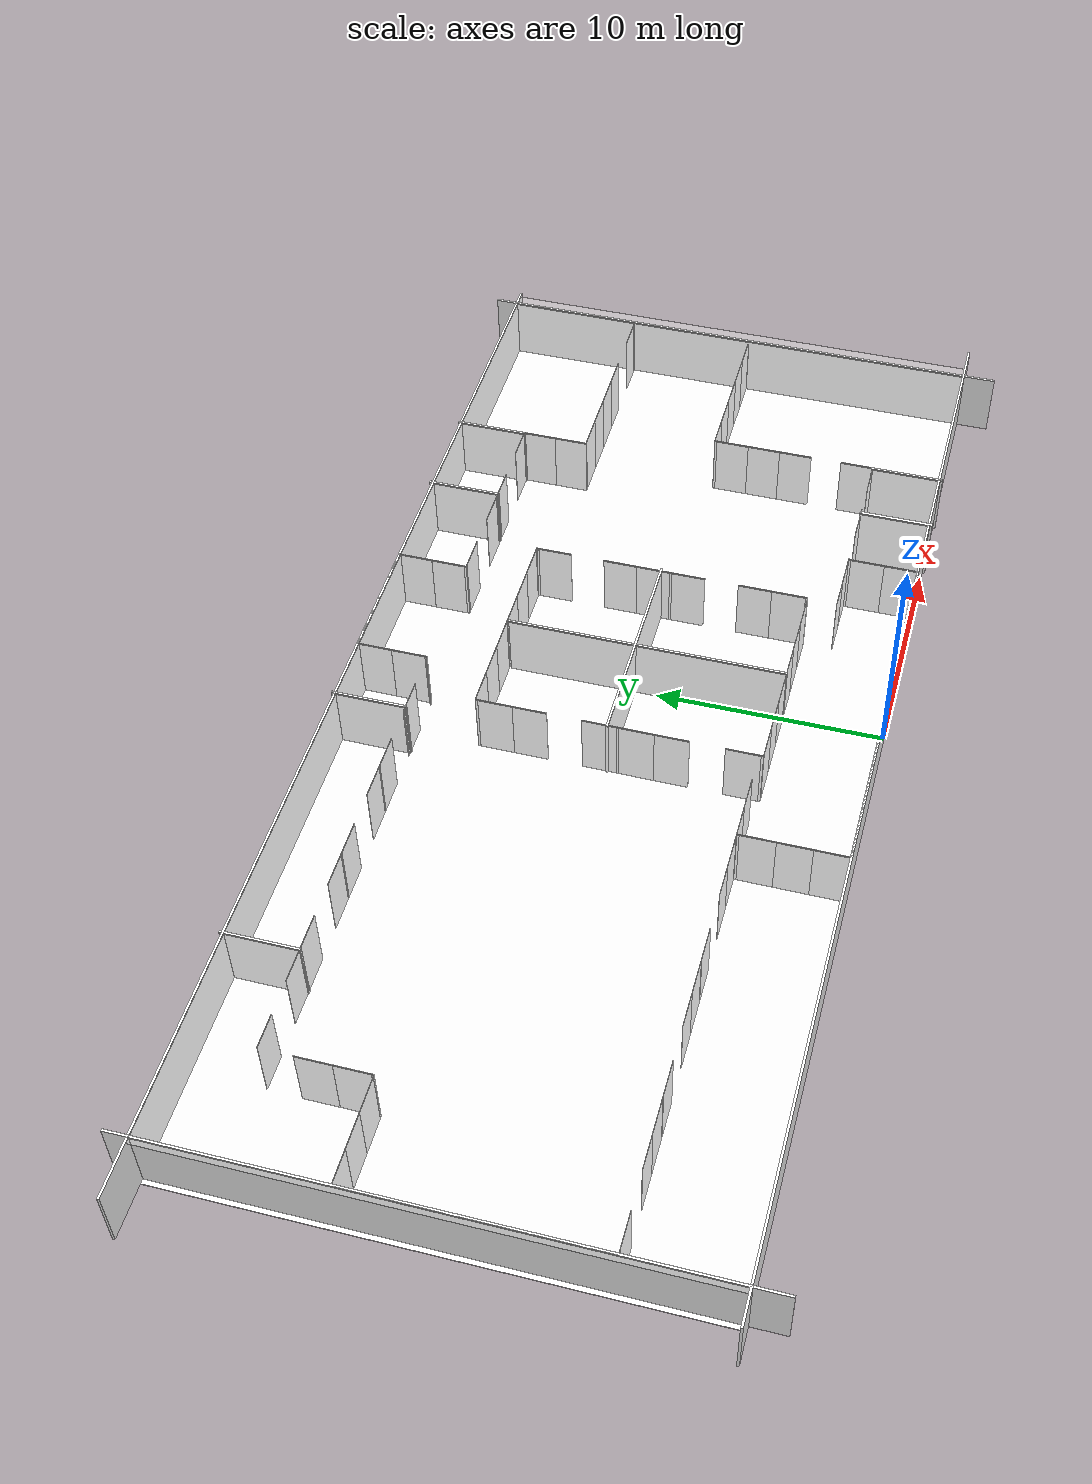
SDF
<sdf version="1.6">
 <world name="default">
  <gravity>0 0 -9.8</gravity>
  <magnetic_field>6e-06 2.3e-05 -4.2e-05</magnetic_field>
  <atmosphere type="adiabatic"/>
  <physics name="default_physics" default="0" type="ode">
   <max_step_size>0.001</max_step_size>
   <real_time_factor>1</real_time_factor>
   <real_time_update_rate>1000</real_time_update_rate>
  </physics>
  <scene>
   <ambient>0.4 0.4 0.4 1</ambient>
   <background>0.7 0.7 0.7 1</background>
   <shadows>false</shadows>
   <grid>false</grid>
   <origin_visual>false</origin_visual>
  </scene>
  <spherical_coordinates>
   <surface_model>EARTH_WGS84</surface_model>
   <latitude_deg>0</latitude_deg>
   <longitude_deg>0</longitude_deg>
   <elevation>0</elevation>
   <heading_deg>0</heading_deg>
  </spherical_coordinates>
  <light name="directional_light" type="directional">
   <pose>0.0 0.0 -100.0 0 0 0</pose>
   <diffuse>0.5 0.5 0.5 1</diffuse>
   <specular>0.1 0.1 0.1 1</specular>
   <direction>0.1 0.1 -0.9</direction>
   <attenuation>
    <range>20</range>
    <constant>0.5</constant>
    <linear>0.01</linear>
    <quadratic>0.001</quadratic>
   </attenuation>
   <cast_shadows>0</cast_shadows>
  </light>
  <plugin filename="gz-sim-physics-system" name="gz::sim::systems::Physics"/>
  <plugin filename="gz-sim-user-commands-system" name="gz::sim::systems::UserCommands"/>
  <plugin filename="gz-sim-scene-broadcaster-system" name="gz::sim::systems::SceneBroadcaster"/>
  <plugin filename="gz-sim-imu-system" name="gz::sim::systems::Imu"/>
  <plugin filename="gz-sim-sensors-system" name="gz::sim::systems::Sensors">
   <render_engine>ogre2</render_engine>
  </plugin>
  <model name="ceiling">
   <pose>-2.9699999999999998        11.25        3.0        0        3.141592653589793        0</pose>
   <static>true</static>
   <link name="link">
    <visual name="visual">
     <geometry><plane><normal>0 0 1</normal><size>49.5 22.5</size></plane></geometry>
     <material>
      <ambient>1 1 1 1</ambient>
      <diffuse>1 1 1 1</diffuse>
      <specular>0.2 0.2 0.2 1</specular>
      <pbr>
       <metal>
        <albedo_map>../media/materials/textures/ceiling.png</albedo_map>
        <metalness>0.0</metalness>
        <roughness>0.9</roughness>
       </metal>
      </pbr>
     </material>
    </visual>
   </link>
  </model>
  <model name="floor">
   <pose>-2.9699999999999998        11.25        -0.001        0        0        0</pose>
   <static>true</static>
   <link name="link">
    <visual name="visual">
     <geometry><plane><normal>0 0 1</normal><size>49.5 22.5</size></plane></geometry>
     <material>
      <ambient>1 1 1 1</ambient>
      <diffuse>1 1 1 1</diffuse>
      <specular>0.2 0.2 0.2 1</specular>
      <pbr>
       <metal>
        <albedo_map>../media/materials/textures/hallway.png</albedo_map>
        <metalness>0.0</metalness>
        <roughness>0.9</roughness>
       </metal>
      </pbr>
     </material>
    </visual>
    <collision name="collision">
     <geometry><plane><normal>0 0 1</normal><size>49.5 22.5</size></plane></geometry>
     <surface><friction><ode><mu>1</mu><mu2>1</mu2></ode></friction></surface>
    </collision>
   </link>
  </model>
  <model name="walls">
   <static>true</static>
   <link name="link">
    <visual name="visual_1">
     <pose>-8.25          0.0          1.5          0.0          0.0          0</pose>
     <geometry><box><size>1.5              0.01              3.0</size></box></geometry>
     <material>
      <ambient>1 1 1 1</ambient>
      <diffuse>1 1 1 1</diffuse>
      <specular>0.2 0.2 0.2 1</specular>
      <pbr>
       <metal>
        <albedo_map>../media/materials/textures/plain.png</albedo_map>
        <metalness>0.0</metalness>
        <roughness>0.9</roughness>
       </metal>
      </pbr>
     </material>
    </visual>
    <collision name="collision_1">
     <pose>-8.25          0.0          1.5          0.0          0.0          0</pose>
     <geometry><box><size>1.5              0.01              3.0</size></box></geometry>
    </collision>
    <visual name="visual_2">
     <pose>-6.75          0.0          1.5          0.0          0.0          0</pose>
     <geometry><box><size>1.5              0.01              3.0</size></box></geometry>
     <material>
      <ambient>1 1 1 1</ambient>
      <diffuse>1 1 1 1</diffuse>
      <specular>0.2 0.2 0.2 1</specular>
      <pbr>
       <metal>
        <albedo_map>../media/materials/textures/plain.png</albedo_map>
        <metalness>0.0</metalness>
        <roughness>0.9</roughness>
       </metal>
      </pbr>
     </material>
    </visual>
    <collision name="collision_2">
     <pose>-6.75          0.0          1.5          0.0          0.0          0</pose>
     <geometry><box><size>1.5              0.01              3.0</size></box></geometry>
    </collision>
    <visual name="visual_3">
     <pose>-5.25          0.0          1.5          0.0          0.0          0</pose>
     <geometry><box><size>1.5              0.01              3.0</size></box></geometry>
     <material>
      <ambient>1 1 1 1</ambient>
      <diffuse>1 1 1 1</diffuse>
      <specular>0.2 0.2 0.2 1</specular>
      <pbr>
       <metal>
        <albedo_map>../media/materials/textures/plain.png</albedo_map>
        <metalness>0.0</metalness>
        <roughness>0.9</roughness>
       </metal>
      </pbr>
     </material>
    </visual>
    <collision name="collision_3">
     <pose>-5.25          0.0          1.5          0.0          0.0          0</pose>
     <geometry><box><size>1.5              0.01              3.0</size></box></geometry>
    </collision>
    <visual name="visual_4">
     <pose>-3.75          0.0          1.5          0.0          0.0          0</pose>
     <geometry><box><size>1.5              0.01              3.0</size></box></geometry>
     <material>
      <ambient>1 1 1 1</ambient>
      <diffuse>1 1 1 1</diffuse>
      <specular>0.2 0.2 0.2 1</specular>
      <pbr>
       <metal>
        <albedo_map>../media/materials/textures/plain.png</albedo_map>
        <metalness>0.0</metalness>
        <roughness>0.9</roughness>
       </metal>
      </pbr>
     </material>
    </visual>
    <collision name="collision_4">
     <pose>-3.75          0.0          1.5          0.0          0.0          0</pose>
     <geometry><box><size>1.5              0.01              3.0</size></box></geometry>
    </collision>
    <visual name="visual_5">
     <pose>-2.25          0.0          1.5          0.0          0.0          0</pose>
     <geometry><box><size>1.5              0.01              3.0</size></box></geometry>
     <material>
      <ambient>1 1 1 1</ambient>
      <diffuse>1 1 1 1</diffuse>
      <specular>0.2 0.2 0.2 1</specular>
      <pbr>
       <metal>
        <albedo_map>../media/materials/textures/plain.png</albedo_map>
        <metalness>0.0</metalness>
        <roughness>0.9</roughness>
       </metal>
      </pbr>
     </material>
    </visual>
    <collision name="collision_5">
     <pose>-2.25          0.0          1.5          0.0          0.0          0</pose>
     <geometry><box><size>1.5              0.01              3.0</size></box></geometry>
    </collision>
    <visual name="visual_6">
     <pose>-0.75          0.0          1.5          0.0          0.0          0</pose>
     <geometry><box><size>1.5              0.01              3.0</size></box></geometry>
     <material>
      <ambient>1 1 1 1</ambient>
      <diffuse>1 1 1 1</diffuse>
      <specular>0.2 0.2 0.2 1</specular>
      <pbr>
       <metal>
        <albedo_map>../media/materials/textures/elevator.png</albedo_map>
        <metalness>0.0</metalness>
        <roughness>0.9</roughness>
       </metal>
      </pbr>
     </material>
    </visual>
    <collision name="collision_6">
     <pose>-0.75          0.0          1.5          0.0          0.0          0</pose>
     <geometry><box><size>1.5              0.01              3.0</size></box></geometry>
    </collision>
    <visual name="visual_7">
     <pose>0.75          0.0          1.5          0.0          0.0          0</pose>
     <geometry><box><size>1.5              0.01              3.0</size></box></geometry>
     <material>
      <ambient>1 1 1 1</ambient>
      <diffuse>1 1 1 1</diffuse>
      <specular>0.2 0.2 0.2 1</specular>
      <pbr>
       <metal>
        <albedo_map>../media/materials/textures/elevator.png</albedo_map>
        <metalness>0.0</metalness>
        <roughness>0.9</roughness>
       </metal>
      </pbr>
     </material>
    </visual>
    <collision name="collision_7">
     <pose>0.75          0.0          1.5          0.0          0.0          0</pose>
     <geometry><box><size>1.5              0.01              3.0</size></box></geometry>
    </collision>
    <visual name="visual_8">
     <pose>2.25          0.0          1.5          0.0          0.0          0</pose>
     <geometry><box><size>1.5              0.01              3.0</size></box></geometry>
     <material>
      <ambient>1 1 1 1</ambient>
      <diffuse>1 1 1 1</diffuse>
      <specular>0.2 0.2 0.2 1</specular>
      <pbr>
       <metal>
        <albedo_map>../media/materials/textures/plain.png</albedo_map>
        <metalness>0.0</metalness>
        <roughness>0.9</roughness>
       </metal>
      </pbr>
     </material>
    </visual>
    <collision name="collision_8">
     <pose>2.25          0.0          1.5          0.0          0.0          0</pose>
     <geometry><box><size>1.5              0.01              3.0</size></box></geometry>
    </collision>
    <visual name="visual_9">
     <pose>3.75          0.0          1.5          0.0          0.0          0</pose>
     <geometry><box><size>1.5              0.01              3.0</size></box></geometry>
     <material>
      <ambient>1 1 1 1</ambient>
      <diffuse>1 1 1 1</diffuse>
      <specular>0.2 0.2 0.2 1</specular>
      <pbr>
       <metal>
        <albedo_map>../media/materials/textures/plain.png</albedo_map>
        <metalness>0.0</metalness>
        <roughness>0.9</roughness>
       </metal>
      </pbr>
     </material>
    </visual>
    <collision name="collision_9">
     <pose>3.75          0.0          1.5          0.0          0.0          0</pose>
     <geometry><box><size>1.5              0.01              3.0</size></box></geometry>
    </collision>
    <visual name="visual_10">
     <pose>5.25          0.0          1.5          0.0          0.0          0</pose>
     <geometry><box><size>1.5              0.01              3.0</size></box></geometry>
     <material>
      <ambient>1 1 1 1</ambient>
      <diffuse>1 1 1 1</diffuse>
      <specular>0.2 0.2 0.2 1</specular>
      <pbr>
       <metal>
        <albedo_map>../media/materials/textures/plain.png</albedo_map>
        <metalness>0.0</metalness>
        <roughness>0.9</roughness>
       </metal>
      </pbr>
     </material>
    </visual>
    <collision name="collision_10">
     <pose>5.25          0.0          1.5          0.0          0.0          0</pose>
     <geometry><box><size>1.5              0.01              3.0</size></box></geometry>
    </collision>
    <visual name="visual_11">
     <pose>6.749          0.0          1.5          0.0          0.0          0</pose>
     <geometry><box><size>1.5              0.01              3.0</size></box></geometry>
     <material>
      <ambient>1 1 1 1</ambient>
      <diffuse>1 1 1 1</diffuse>
      <specular>0.2 0.2 0.2 1</specular>
      <pbr>
       <metal>
        <albedo_map>../media/materials/textures/plain.png</albedo_map>
        <metalness>0.0</metalness>
        <roughness>0.9</roughness>
       </metal>
      </pbr>
     </material>
    </visual>
    <collision name="collision_11">
     <pose>6.749          0.0          1.5          0.0          0.0          0</pose>
     <geometry><box><size>1.5              0.01              3.0</size></box></geometry>
    </collision>
    <visual name="visual_12">
     <pose>-8.25          4.6          1.5          0.0          0.0          0</pose>
     <geometry><box><size>1.5              0.01              3.0</size></box></geometry>
     <material>
      <ambient>1 1 1 1</ambient>
      <diffuse>1 1 1 1</diffuse>
      <specular>0.2 0.2 0.2 1</specular>
      <pbr>
       <metal>
        <albedo_map>../media/materials/textures/plain.png</albedo_map>
        <metalness>0.0</metalness>
        <roughness>0.9</roughness>
       </metal>
      </pbr>
     </material>
    </visual>
    <collision name="collision_12">
     <pose>-8.25          4.6          1.5          0.0          0.0          0</pose>
     <geometry><box><size>1.5              0.01              3.0</size></box></geometry>
    </collision>
    <visual name="visual_13">
     <pose>-6.75          4.6          1.5          0.0          0.0          0</pose>
     <geometry><box><size>1.5              0.01              3.0</size></box></geometry>
     <material>
      <ambient>1 1 1 1</ambient>
      <diffuse>1 1 1 1</diffuse>
      <specular>0.2 0.2 0.2 1</specular>
      <pbr>
       <metal>
        <albedo_map>../media/materials/textures/plain.png</albedo_map>
        <metalness>0.0</metalness>
        <roughness>0.9</roughness>
       </metal>
      </pbr>
     </material>
    </visual>
    <collision name="collision_13">
     <pose>-6.75          4.6          1.5          0.0          0.0          0</pose>
     <geometry><box><size>1.5              0.01              3.0</size></box></geometry>
    </collision>
    <visual name="visual_14">
     <pose>5.25          3.1          1.5          0.0          0.0          0</pose>
     <geometry><box><size>1.5              0.01              3.0</size></box></geometry>
     <material>
      <ambient>1 1 1 1</ambient>
      <diffuse>1 1 1 1</diffuse>
      <specular>0.2 0.2 0.2 1</specular>
      <pbr>
       <metal>
        <albedo_map>../media/materials/textures/plain.png</albedo_map>
        <metalness>0.0</metalness>
        <roughness>0.9</roughness>
       </metal>
      </pbr>
     </material>
    </visual>
    <collision name="collision_14">
     <pose>5.25          3.1          1.5          0.0          0.0          0</pose>
     <geometry><box><size>1.5              0.01              3.0</size></box></geometry>
    </collision>
    <visual name="visual_15">
     <pose>6.75          3.1          1.5          0.0          0.0          0</pose>
     <geometry><box><size>1.5              0.01              3.0</size></box></geometry>
     <material>
      <ambient>1 1 1 1</ambient>
      <diffuse>1 1 1 1</diffuse>
      <specular>0.2 0.2 0.2 1</specular>
      <pbr>
       <metal>
        <albedo_map>../media/materials/textures/plain.png</albedo_map>
        <metalness>0.0</metalness>
        <roughness>0.9</roughness>
       </metal>
      </pbr>
     </material>
    </visual>
    <collision name="collision_15">
     <pose>6.75          3.1          1.5          0.0          0.0          0</pose>
     <geometry><box><size>1.5              0.01              3.0</size></box></geometry>
    </collision>
    <visual name="visual_16">
     <pose>7.4          0.75          1.5          0.0          0.0          1.5707963267948966</pose>
     <geometry><box><size>1.5              0.01              3.0</size></box></geometry>
     <material>
      <ambient>1 1 1 1</ambient>
      <diffuse>1 1 1 1</diffuse>
      <specular>0.2 0.2 0.2 1</specular>
      <pbr>
       <metal>
        <albedo_map>../media/materials/textures/plain.png</albedo_map>
        <metalness>0.0</metalness>
        <roughness>0.9</roughness>
       </metal>
      </pbr>
     </material>
    </visual>
    <collision name="collision_16">
     <pose>7.4          0.75          1.5          0.0          0.0          1.5707963267948966</pose>
     <geometry><box><size>1.5              0.01              3.0</size></box></geometry>
    </collision>
    <visual name="visual_17">
     <pose>7.4          2.25          1.5          0.0          0.0          1.5707963267948966</pose>
     <geometry><box><size>1.5              0.01              3.0</size></box></geometry>
     <material>
      <ambient>1 1 1 1</ambient>
      <diffuse>1 1 1 1</diffuse>
      <specular>0.2 0.2 0.2 1</specular>
      <pbr>
       <metal>
        <albedo_map>../media/materials/textures/plain.png</albedo_map>
        <metalness>0.0</metalness>
        <roughness>0.9</roughness>
       </metal>
      </pbr>
     </material>
    </visual>
    <collision name="collision_17">
     <pose>7.4          2.25          1.5          0.0          0.0          1.5707963267948966</pose>
     <geometry><box><size>1.5              0.01              3.0</size></box></geometry>
    </collision>
    <visual name="visual_18">
     <pose>7.4          3.05          1.5          0.0          0.0          1.5707963267948966</pose>
     <geometry><box><size>0.1              0.01              3.0</size></box></geometry>
     <material>
      <ambient>1 1 1 1</ambient>
      <diffuse>1 1 1 1</diffuse>
      <specular>0.2 0.2 0.2 1</specular>
      <pbr>
       <metal>
        <albedo_map>../media/materials/textures/plain.png</albedo_map>
        <metalness>0.0</metalness>
        <roughness>0.9</roughness>
       </metal>
      </pbr>
     </material>
    </visual>
    <collision name="collision_18">
     <pose>7.4          3.05          1.5          0.0          0.0          1.5707963267948966</pose>
     <geometry><box><size>0.1              0.01              3.0</size></box></geometry>
    </collision>
    <visual name="visual_19">
     <pose>7.45          3.1          1.5          0.0          0.0          0</pose>
     <geometry><box><size>0.1              0.01              3.0</size></box></geometry>
     <material>
      <ambient>1 1 1 1</ambient>
      <diffuse>1 1 1 1</diffuse>
      <specular>0.2 0.2 0.2 1</specular>
      <pbr>
       <metal>
        <albedo_map>../media/materials/textures/plain.png</albedo_map>
        <metalness>0.0</metalness>
        <roughness>0.9</roughness>
       </metal>
      </pbr>
     </material>
    </visual>
    <collision name="collision_19">
     <pose>7.45          3.1          1.5          0.0          0.0          0</pose>
     <geometry><box><size>0.1              0.01              3.0</size></box></geometry>
    </collision>
    <visual name="visual_20">
     <pose>7.55          3.1          1.5          0.0          0.0          0</pose>
     <geometry><box><size>0.1              0.01              3.0</size></box></geometry>
     <material>
      <ambient>1 1 1 1</ambient>
      <diffuse>1 1 1 1</diffuse>
      <specular>0.2 0.2 0.2 1</specular>
      <pbr>
       <metal>
        <albedo_map>../media/materials/textures/plain.png</albedo_map>
        <metalness>0.0</metalness>
        <roughness>0.9</roughness>
       </metal>
      </pbr>
     </material>
    </visual>
    <collision name="collision_20">
     <pose>7.55          3.1          1.5          0.0          0.0          0</pose>
     <geometry><box><size>0.1              0.01              3.0</size></box></geometry>
    </collision>
    <visual name="visual_21">
     <pose>9.75          3.1          1.5          0.0          0.0          0</pose>
     <geometry><box><size>1.5              0.01              3.0</size></box></geometry>
     <material>
      <ambient>1 1 1 1</ambient>
      <diffuse>1 1 1 1</diffuse>
      <specular>0.2 0.2 0.2 1</specular>
      <pbr>
       <metal>
        <albedo_map>../media/materials/textures/plain.png</albedo_map>
        <metalness>0.0</metalness>
        <roughness>0.9</roughness>
       </metal>
      </pbr>
     </material>
    </visual>
    <collision name="collision_21">
     <pose>9.75          3.1          1.5          0.0          0.0          0</pose>
     <geometry><box><size>1.5              0.01              3.0</size></box></geometry>
    </collision>
    <visual name="visual_22">
     <pose>10.55          3.1          1.5          0.0          0.0          0</pose>
     <geometry><box><size>0.1              0.01              3.0</size></box></geometry>
     <material>
      <ambient>1 1 1 1</ambient>
      <diffuse>1 1 1 1</diffuse>
      <specular>0.2 0.2 0.2 1</specular>
      <pbr>
       <metal>
        <albedo_map>../media/materials/textures/plain.png</albedo_map>
        <metalness>0.0</metalness>
        <roughness>0.9</roughness>
       </metal>
      </pbr>
     </material>
    </visual>
    <collision name="collision_22">
     <pose>10.55          3.1          1.5          0.0          0.0          0</pose>
     <geometry><box><size>0.1              0.01              3.0</size></box></geometry>
    </collision>
    <visual name="visual_23">
     <pose>10.65          3.1          1.5          0.0          0.0          0</pose>
     <geometry><box><size>0.1              0.01              3.0</size></box></geometry>
     <material>
      <ambient>1 1 1 1</ambient>
      <diffuse>1 1 1 1</diffuse>
      <specular>0.2 0.2 0.2 1</specular>
      <pbr>
       <metal>
        <albedo_map>../media/materials/textures/plain.png</albedo_map>
        <metalness>0.0</metalness>
        <roughness>0.9</roughness>
       </metal>
      </pbr>
     </material>
    </visual>
    <collision name="collision_23">
     <pose>10.65          3.1          1.5          0.0          0.0          0</pose>
     <geometry><box><size>0.1              0.01              3.0</size></box></geometry>
    </collision>
    <visual name="visual_24">
     <pose>12.85          3.1          1.5          0.0          0.0          0</pose>
     <geometry><box><size>1.5              0.01              3.0</size></box></geometry>
     <material>
      <ambient>1 1 1 1</ambient>
      <diffuse>1 1 1 1</diffuse>
      <specular>0.2 0.2 0.2 1</specular>
      <pbr>
       <metal>
        <albedo_map>../media/materials/textures/plain.png</albedo_map>
        <metalness>0.0</metalness>
        <roughness>0.9</roughness>
       </metal>
      </pbr>
     </material>
    </visual>
    <collision name="collision_24">
     <pose>12.85          3.1          1.5          0.0          0.0          0</pose>
     <geometry><box><size>1.5              0.01              3.0</size></box></geometry>
    </collision>
    <visual name="visual_25">
     <pose>13.6          3.85          1.5          0.0          0.0          1.5707963267948966</pose>
     <geometry><box><size>1.5              0.01              3.0</size></box></geometry>
     <material>
      <ambient>1 1 1 1</ambient>
      <diffuse>1 1 1 1</diffuse>
      <specular>0.2 0.2 0.2 1</specular>
      <pbr>
       <metal>
        <albedo_map>../media/materials/textures/plain.png</albedo_map>
        <metalness>0.0</metalness>
        <roughness>0.9</roughness>
       </metal>
      </pbr>
     </material>
    </visual>
    <collision name="collision_25">
     <pose>13.6          3.85          1.5          0.0          0.0          1.5707963267948966</pose>
     <geometry><box><size>1.5              0.01              3.0</size></box></geometry>
    </collision>
    <visual name="visual_26">
     <pose>13.6          6.75          1.5          0.0          0.0          1.5707963267948966</pose>
     <geometry><box><size>1.5              0.01              3.0</size></box></geometry>
     <material>
      <ambient>1 1 1 1</ambient>
      <diffuse>1 1 1 1</diffuse>
      <specular>0.2 0.2 0.2 1</specular>
      <pbr>
       <metal>
        <albedo_map>../media/materials/textures/plain.png</albedo_map>
        <metalness>0.0</metalness>
        <roughness>0.9</roughness>
       </metal>
      </pbr>
     </material>
    </visual>
    <collision name="collision_26">
     <pose>13.6          6.75          1.5          0.0          0.0          1.5707963267948966</pose>
     <geometry><box><size>1.5              0.01              3.0</size></box></geometry>
    </collision>
    <visual name="visual_27">
     <pose>13.6          8.25          1.5          0.0          0.0          1.5707963267948966</pose>
     <geometry><box><size>1.5              0.01              3.0</size></box></geometry>
     <material>
      <ambient>1 1 1 1</ambient>
      <diffuse>1 1 1 1</diffuse>
      <specular>0.2 0.2 0.2 1</specular>
      <pbr>
       <metal>
        <albedo_map>../media/materials/textures/plain.png</albedo_map>
        <metalness>0.0</metalness>
        <roughness>0.9</roughness>
       </metal>
      </pbr>
     </material>
    </visual>
    <collision name="collision_27">
     <pose>13.6          8.25          1.5          0.0          0.0          1.5707963267948966</pose>
     <geometry><box><size>1.5              0.01              3.0</size></box></geometry>
    </collision>
    <visual name="visual_28">
     <pose>13.6          9.75          1.5          0.0          0.0          1.5707963267948966</pose>
     <geometry><box><size>1.5              0.01              3.0</size></box></geometry>
     <material>
      <ambient>1 1 1 1</ambient>
      <diffuse>1 1 1 1</diffuse>
      <specular>0.2 0.2 0.2 1</specular>
      <pbr>
       <metal>
        <albedo_map>../media/materials/textures/plain.png</albedo_map>
        <metalness>0.0</metalness>
        <roughness>0.9</roughness>
       </metal>
      </pbr>
     </material>
    </visual>
    <collision name="collision_28">
     <pose>13.6          9.75          1.5          0.0          0.0          1.5707963267948966</pose>
     <geometry><box><size>1.5              0.01              3.0</size></box></geometry>
    </collision>
    <visual name="visual_29">
     <pose>13.6          10.55          1.5          0.0          0.0          1.5707963267948966</pose>
     <geometry><box><size>0.1              0.01              3.0</size></box></geometry>
     <material>
      <ambient>1 1 1 1</ambient>
      <diffuse>1 1 1 1</diffuse>
      <specular>0.2 0.2 0.2 1</specular>
      <pbr>
       <metal>
        <albedo_map>../media/materials/textures/plain.png</albedo_map>
        <metalness>0.0</metalness>
        <roughness>0.9</roughness>
       </metal>
      </pbr>
     </material>
    </visual>
    <collision name="collision_29">
     <pose>13.6          10.55          1.5          0.0          0.0          1.5707963267948966</pose>
     <geometry><box><size>0.1              0.01              3.0</size></box></geometry>
    </collision>
    <visual name="visual_30">
     <pose>14.35          10.6          1.5          0.0          0.0          0</pose>
     <geometry><box><size>1.5              0.01              3.0</size></box></geometry>
     <material>
      <ambient>1 1 1 1</ambient>
      <diffuse>1 1 1 1</diffuse>
      <specular>0.2 0.2 0.2 1</specular>
      <pbr>
       <metal>
        <albedo_map>../media/materials/textures/plain.png</albedo_map>
        <metalness>0.0</metalness>
        <roughness>0.9</roughness>
       </metal>
      </pbr>
     </material>
    </visual>
    <collision name="collision_30">
     <pose>14.35          10.6          1.5          0.0          0.0          0</pose>
     <geometry><box><size>1.5              0.01              3.0</size></box></geometry>
    </collision>
    <visual name="visual_31">
     <pose>15.85          10.6          1.5          0.0          0.0          0</pose>
     <geometry><box><size>1.5              0.01              3.0</size></box></geometry>
     <material>
      <ambient>1 1 1 1</ambient>
      <diffuse>1 1 1 1</diffuse>
      <specular>0.2 0.2 0.2 1</specular>
      <pbr>
       <metal>
        <albedo_map>../media/materials/textures/plain.png</albedo_map>
        <metalness>0.0</metalness>
        <roughness>0.9</roughness>
       </metal>
      </pbr>
     </material>
    </visual>
    <collision name="collision_31">
     <pose>15.85          10.6          1.5          0.0          0.0          0</pose>
     <geometry><box><size>1.5              0.01              3.0</size></box></geometry>
    </collision>
    <visual name="visual_32">
     <pose>17.35          10.6          1.5          0.0          0.0          0</pose>
     <geometry><box><size>1.5              0.01              3.0</size></box></geometry>
     <material>
      <ambient>1 1 1 1</ambient>
      <diffuse>1 1 1 1</diffuse>
      <specular>0.2 0.2 0.2 1</specular>
      <pbr>
       <metal>
        <albedo_map>../media/materials/textures/plain.png</albedo_map>
        <metalness>0.0</metalness>
        <roughness>0.9</roughness>
       </metal>
      </pbr>
     </material>
    </visual>
    <collision name="collision_32">
     <pose>17.35          10.6          1.5          0.0          0.0          0</pose>
     <geometry><box><size>1.5              0.01              3.0</size></box></geometry>
    </collision>
    <visual name="visual_33">
     <pose>18.85          10.6          1.5          0.0          0.0          0</pose>
     <geometry><box><size>1.5              0.01              3.0</size></box></geometry>
     <material>
      <ambient>1 1 1 1</ambient>
      <diffuse>1 1 1 1</diffuse>
      <specular>0.2 0.2 0.2 1</specular>
      <pbr>
       <metal>
        <albedo_map>../media/materials/textures/plain.png</albedo_map>
        <metalness>0.0</metalness>
        <roughness>0.9</roughness>
       </metal>
      </pbr>
     </material>
    </visual>
    <collision name="collision_33">
     <pose>18.85          10.6          1.5          0.0          0.0          0</pose>
     <geometry><box><size>1.5              0.01              3.0</size></box></geometry>
    </collision>
    <visual name="visual_34">
     <pose>20.35          10.6          1.5          0.0          0.0          0</pose>
     <geometry><box><size>1.5              0.01              3.0</size></box></geometry>
     <material>
      <ambient>1 1 1 1</ambient>
      <diffuse>1 1 1 1</diffuse>
      <specular>0.2 0.2 0.2 1</specular>
      <pbr>
       <metal>
        <albedo_map>../media/materials/textures/plain.png</albedo_map>
        <metalness>0.0</metalness>
        <roughness>0.9</roughness>
       </metal>
      </pbr>
     </material>
    </visual>
    <collision name="collision_34">
     <pose>20.35          10.6          1.5          0.0          0.0          0</pose>
     <geometry><box><size>1.5              0.01              3.0</size></box></geometry>
    </collision>
    <visual name="visual_35">
     <pose>21.150000000000002          10.6          1.5          0.0          0.0          0</pose>
     <geometry><box><size>0.1              0.01              3.0</size></box></geometry>
     <material>
      <ambient>1 1 1 1</ambient>
      <diffuse>1 1 1 1</diffuse>
      <specular>0.2 0.2 0.2 1</specular>
      <pbr>
       <metal>
        <albedo_map>../media/materials/textures/plain.png</albedo_map>
        <metalness>0.0</metalness>
        <roughness>0.9</roughness>
       </metal>
      </pbr>
     </material>
    </visual>
    <collision name="collision_35">
     <pose>21.150000000000002          10.6          1.5          0.0          0.0          0</pose>
     <geometry><box><size>0.1              0.01              3.0</size></box></geometry>
    </collision>
    <visual name="visual_36">
     <pose>21.2          11.35          1.5          0.0          0.0          1.5707963267948966</pose>
     <geometry><box><size>1.5              0.01              3.0</size></box></geometry>
     <material>
      <ambient>1 1 1 1</ambient>
      <diffuse>1 1 1 1</diffuse>
      <specular>0.2 0.2 0.2 1</specular>
      <pbr>
       <metal>
        <albedo_map>../media/materials/textures/plain.png</albedo_map>
        <metalness>0.0</metalness>
        <roughness>0.9</roughness>
       </metal>
      </pbr>
     </material>
    </visual>
    <collision name="collision_36">
     <pose>21.2          11.35          1.5          0.0          0.0          1.5707963267948966</pose>
     <geometry><box><size>1.5              0.01              3.0</size></box></geometry>
    </collision>
    <visual name="visual_37">
     <pose>21.2          12.85          1.5          0.0          0.0          1.5707963267948966</pose>
     <geometry><box><size>1.5              0.01              3.0</size></box></geometry>
     <material>
      <ambient>1 1 1 1</ambient>
      <diffuse>1 1 1 1</diffuse>
      <specular>0.2 0.2 0.2 1</specular>
      <pbr>
       <metal>
        <albedo_map>../media/materials/textures/plain.png</albedo_map>
        <metalness>0.0</metalness>
        <roughness>0.9</roughness>
       </metal>
      </pbr>
     </material>
    </visual>
    <collision name="collision_37">
     <pose>21.2          12.85          1.5          0.0          0.0          1.5707963267948966</pose>
     <geometry><box><size>1.5              0.01              3.0</size></box></geometry>
    </collision>
    <visual name="visual_38">
     <pose>21.2          14.35          1.5          0.0          0.0          1.5707963267948966</pose>
     <geometry><box><size>1.5              0.01              3.0</size></box></geometry>
     <material>
      <ambient>1 1 1 1</ambient>
      <diffuse>1 1 1 1</diffuse>
      <specular>0.2 0.2 0.2 1</specular>
      <pbr>
       <metal>
        <albedo_map>../media/materials/textures/plain.png</albedo_map>
        <metalness>0.0</metalness>
        <roughness>0.9</roughness>
       </metal>
      </pbr>
     </material>
    </visual>
    <collision name="collision_38">
     <pose>21.2          14.35          1.5          0.0          0.0          1.5707963267948966</pose>
     <geometry><box><size>1.5              0.01              3.0</size></box></geometry>
    </collision>
    <visual name="visual_39">
     <pose>21.2          15.85          1.5          0.0          0.0          1.5707963267948966</pose>
     <geometry><box><size>1.5              0.01              3.0</size></box></geometry>
     <material>
      <ambient>1 1 1 1</ambient>
      <diffuse>1 1 1 1</diffuse>
      <specular>0.2 0.2 0.2 1</specular>
      <pbr>
       <metal>
        <albedo_map>../media/materials/textures/plain.png</albedo_map>
        <metalness>0.0</metalness>
        <roughness>0.9</roughness>
       </metal>
      </pbr>
     </material>
    </visual>
    <collision name="collision_39">
     <pose>21.2          15.85          1.5          0.0          0.0          1.5707963267948966</pose>
     <geometry><box><size>1.5              0.01              3.0</size></box></geometry>
    </collision>
    <visual name="visual_40">
     <pose>20.95          16.4          1.5          0.0          0.0          0</pose>
     <geometry><box><size>0.1              0.01              3.0</size></box></geometry>
     <material>
      <ambient>1 1 1 1</ambient>
      <diffuse>1 1 1 1</diffuse>
      <specular>0.2 0.2 0.2 1</specular>
      <pbr>
       <metal>
        <albedo_map>../media/materials/textures/plain.png</albedo_map>
        <metalness>0.0</metalness>
        <roughness>0.9</roughness>
       </metal>
      </pbr>
     </material>
    </visual>
    <collision name="collision_40">
     <pose>20.95          16.4          1.5          0.0          0.0          0</pose>
     <geometry><box><size>0.1              0.01              3.0</size></box></geometry>
    </collision>
    <visual name="visual_41">
     <pose>21.05          16.4          1.5          0.0          0.0          0</pose>
     <geometry><box><size>0.1              0.01              3.0</size></box></geometry>
     <material>
      <ambient>1 1 1 1</ambient>
      <diffuse>1 1 1 1</diffuse>
      <specular>0.2 0.2 0.2 1</specular>
      <pbr>
       <metal>
        <albedo_map>../media/materials/textures/plain.png</albedo_map>
        <metalness>0.0</metalness>
        <roughness>0.9</roughness>
       </metal>
      </pbr>
     </material>
    </visual>
    <collision name="collision_41">
     <pose>21.05          16.4          1.5          0.0          0.0          0</pose>
     <geometry><box><size>0.1              0.01              3.0</size></box></geometry>
    </collision>
    <visual name="visual_42">
     <pose>21.150000000000002          16.4          1.5          0.0          0.0          0</pose>
     <geometry><box><size>0.1              0.01              3.0</size></box></geometry>
     <material>
      <ambient>1 1 1 1</ambient>
      <diffuse>1 1 1 1</diffuse>
      <specular>0.2 0.2 0.2 1</specular>
      <pbr>
       <metal>
        <albedo_map>../media/materials/textures/plain.png</albedo_map>
        <metalness>0.0</metalness>
        <roughness>0.9</roughness>
       </metal>
      </pbr>
     </material>
    </visual>
    <collision name="collision_42">
     <pose>21.150000000000002          16.4          1.5          0.0          0.0          0</pose>
     <geometry><box><size>0.1              0.01              3.0</size></box></geometry>
    </collision>
    <visual name="visual_43">
     <pose>20.25          16.4          1.5          0.0          0.0          0</pose>
     <geometry><box><size>1.5              0.01              3.0</size></box></geometry>
     <material>
      <ambient>1 1 1 1</ambient>
      <diffuse>1 1 1 1</diffuse>
      <specular>0.2 0.2 0.2 1</specular>
      <pbr>
       <metal>
        <albedo_map>../media/materials/textures/plain.png</albedo_map>
        <metalness>0.0</metalness>
        <roughness>0.9</roughness>
       </metal>
      </pbr>
     </material>
    </visual>
    <collision name="collision_43">
     <pose>20.25          16.4          1.5          0.0          0.0          0</pose>
     <geometry><box><size>1.5              0.01              3.0</size></box></geometry>
    </collision>
    <visual name="visual_44">
     <pose>17.25          16.4          1.5          0.0          0.0          0</pose>
     <geometry><box><size>1.5              0.01              3.0</size></box></geometry>
     <material>
      <ambient>1 1 1 1</ambient>
      <diffuse>1 1 1 1</diffuse>
      <specular>0.2 0.2 0.2 1</specular>
      <pbr>
       <metal>
        <albedo_map>../media/materials/textures/plain.png</albedo_map>
        <metalness>0.0</metalness>
        <roughness>0.9</roughness>
       </metal>
      </pbr>
     </material>
    </visual>
    <collision name="collision_44">
     <pose>17.25          16.4          1.5          0.0          0.0          0</pose>
     <geometry><box><size>1.5              0.01              3.0</size></box></geometry>
    </collision>
    <visual name="visual_45">
     <pose>15.75          16.4          1.5          0.0          0.0          0</pose>
     <geometry><box><size>1.5              0.01              3.0</size></box></geometry>
     <material>
      <ambient>1 1 1 1</ambient>
      <diffuse>1 1 1 1</diffuse>
      <specular>0.2 0.2 0.2 1</specular>
      <pbr>
       <metal>
        <albedo_map>../media/materials/textures/plain.png</albedo_map>
        <metalness>0.0</metalness>
        <roughness>0.9</roughness>
       </metal>
      </pbr>
     </material>
    </visual>
    <collision name="collision_45">
     <pose>15.75          16.4          1.5          0.0          0.0          0</pose>
     <geometry><box><size>1.5              0.01              3.0</size></box></geometry>
    </collision>
    <visual name="visual_46">
     <pose>14.25          16.4          1.5          0.0          0.0          0</pose>
     <geometry><box><size>1.5              0.01              3.0</size></box></geometry>
     <material>
      <ambient>1 1 1 1</ambient>
      <diffuse>1 1 1 1</diffuse>
      <specular>0.2 0.2 0.2 1</specular>
      <pbr>
       <metal>
        <albedo_map>../media/materials/textures/plain.png</albedo_map>
        <metalness>0.0</metalness>
        <roughness>0.9</roughness>
       </metal>
      </pbr>
     </material>
    </visual>
    <collision name="collision_46">
     <pose>14.25          16.4          1.5          0.0          0.0          0</pose>
     <geometry><box><size>1.5              0.01              3.0</size></box></geometry>
    </collision>
    <visual name="visual_47">
     <pose>12.75          16.4          1.5          0.0          0.0          0</pose>
     <geometry><box><size>1.5              0.01              3.0</size></box></geometry>
     <material>
      <ambient>1 1 1 1</ambient>
      <diffuse>1 1 1 1</diffuse>
      <specular>0.2 0.2 0.2 1</specular>
      <pbr>
       <metal>
        <albedo_map>../media/materials/textures/plain.png</albedo_map>
        <metalness>0.0</metalness>
        <roughness>0.9</roughness>
       </metal>
      </pbr>
     </material>
    </visual>
    <collision name="collision_47">
     <pose>12.75          16.4          1.5          0.0          0.0          0</pose>
     <geometry><box><size>1.5              0.01              3.0</size></box></geometry>
    </collision>
    <visual name="visual_48">
     <pose>11.950000000000001          16.4          1.5          0.0          0.0          0</pose>
     <geometry><box><size>0.1              0.01              3.0</size></box></geometry>
     <material>
      <ambient>1 1 1 1</ambient>
      <diffuse>1 1 1 1</diffuse>
      <specular>0.2 0.2 0.2 1</specular>
      <pbr>
       <metal>
        <albedo_map>../media/materials/textures/plain.png</albedo_map>
        <metalness>0.0</metalness>
        <roughness>0.9</roughness>
       </metal>
      </pbr>
     </material>
    </visual>
    <collision name="collision_48">
     <pose>11.950000000000001          16.4          1.5          0.0          0.0          0</pose>
     <geometry><box><size>0.1              0.01              3.0</size></box></geometry>
    </collision>
    <visual name="visual_49">
     <pose>11.9          17.15          1.5          0.0          0.0          1.5707963267948966</pose>
     <geometry><box><size>1.5              0.01              3.0</size></box></geometry>
     <material>
      <ambient>1 1 1 1</ambient>
      <diffuse>1 1 1 1</diffuse>
      <specular>0.2 0.2 0.2 1</specular>
      <pbr>
       <metal>
        <albedo_map>../media/materials/textures/plain.png</albedo_map>
        <metalness>0.0</metalness>
        <roughness>0.9</roughness>
       </metal>
      </pbr>
     </material>
    </visual>
    <collision name="collision_49">
     <pose>11.9          17.15          1.5          0.0          0.0          1.5707963267948966</pose>
     <geometry><box><size>1.5              0.01              3.0</size></box></geometry>
    </collision>
    <visual name="visual_50">
     <pose>11.9          18.65          1.5          0.0          0.0          1.5707963267948966</pose>
     <geometry><box><size>1.5              0.01              3.0</size></box></geometry>
     <material>
      <ambient>1 1 1 1</ambient>
      <diffuse>1 1 1 1</diffuse>
      <specular>0.2 0.2 0.2 1</specular>
      <pbr>
       <metal>
        <albedo_map>../media/materials/textures/plain.png</albedo_map>
        <metalness>0.0</metalness>
        <roughness>0.9</roughness>
       </metal>
      </pbr>
     </material>
    </visual>
    <collision name="collision_50">
     <pose>11.9          18.65          1.5          0.0          0.0          1.5707963267948966</pose>
     <geometry><box><size>1.5              0.01              3.0</size></box></geometry>
    </collision>
    <visual name="visual_51">
     <pose>11.15          19.4          1.5          0.0          0.0          0</pose>
     <geometry><box><size>1.5              0.01              3.0</size></box></geometry>
     <material>
      <ambient>1 1 1 1</ambient>
      <diffuse>1 1 1 1</diffuse>
      <specular>0.2 0.2 0.2 1</specular>
      <pbr>
       <metal>
        <albedo_map>../media/materials/textures/plain.png</albedo_map>
        <metalness>0.0</metalness>
        <roughness>0.9</roughness>
       </metal>
      </pbr>
     </material>
    </visual>
    <collision name="collision_51">
     <pose>11.15          19.4          1.5          0.0          0.0          0</pose>
     <geometry><box><size>1.5              0.01              3.0</size></box></geometry>
    </collision>
    <visual name="visual_52">
     <pose>8.15          19.4          1.5          0.0          0.0          0</pose>
     <geometry><box><size>1.5              0.01              3.0</size></box></geometry>
     <material>
      <ambient>1 1 1 1</ambient>
      <diffuse>1 1 1 1</diffuse>
      <specular>0.2 0.2 0.2 1</specular>
      <pbr>
       <metal>
        <albedo_map>../media/materials/textures/plain.png</albedo_map>
        <metalness>0.0</metalness>
        <roughness>0.9</roughness>
       </metal>
      </pbr>
     </material>
    </visual>
    <collision name="collision_52">
     <pose>8.15          19.4          1.5          0.0          0.0          0</pose>
     <geometry><box><size>1.5              0.01              3.0</size></box></geometry>
    </collision>
    <visual name="visual_53">
     <pose>7.35          19.4          1.5          0.0          0.0          0</pose>
     <geometry><box><size>0.1              0.01              3.0</size></box></geometry>
     <material>
      <ambient>1 1 1 1</ambient>
      <diffuse>1 1 1 1</diffuse>
      <specular>0.2 0.2 0.2 1</specular>
      <pbr>
       <metal>
        <albedo_map>../media/materials/textures/plain.png</albedo_map>
        <metalness>0.0</metalness>
        <roughness>0.9</roughness>
       </metal>
      </pbr>
     </material>
    </visual>
    <collision name="collision_53">
     <pose>7.35          19.4          1.5          0.0          0.0          0</pose>
     <geometry><box><size>0.1              0.01              3.0</size></box></geometry>
    </collision>
    <visual name="visual_54">
     <pose>6.55          19.4          1.5          0.0          0.0          0</pose>
     <geometry><box><size>1.5              0.01              3.0</size></box></geometry>
     <material>
      <ambient>1 1 1 1</ambient>
      <diffuse>1 1 1 1</diffuse>
      <specular>0.2 0.2 0.2 1</specular>
      <pbr>
       <metal>
        <albedo_map>../media/materials/textures/plain.png</albedo_map>
        <metalness>0.0</metalness>
        <roughness>0.9</roughness>
       </metal>
      </pbr>
     </material>
    </visual>
    <collision name="collision_54">
     <pose>6.55          19.4          1.5          0.0          0.0          0</pose>
     <geometry><box><size>1.5              0.01              3.0</size></box></geometry>
    </collision>
    <visual name="visual_55">
     <pose>3.55          19.4          1.5          0.0          0.0          0</pose>
     <geometry><box><size>1.5              0.01              3.0</size></box></geometry>
     <material>
      <ambient>1 1 1 1</ambient>
      <diffuse>1 1 1 1</diffuse>
      <specular>0.2 0.2 0.2 1</specular>
      <pbr>
       <metal>
        <albedo_map>../media/materials/textures/plain.png</albedo_map>
        <metalness>0.0</metalness>
        <roughness>0.9</roughness>
       </metal>
      </pbr>
     </material>
    </visual>
    <collision name="collision_55">
     <pose>3.55          19.4          1.5          0.0          0.0          0</pose>
     <geometry><box><size>1.5              0.01              3.0</size></box></geometry>
    </collision>
    <visual name="visual_56">
     <pose>2.75          19.4          1.5          0.0          0.0          0</pose>
     <geometry><box><size>0.1              0.01              3.0</size></box></geometry>
     <material>
      <ambient>1 1 1 1</ambient>
      <diffuse>1 1 1 1</diffuse>
      <specular>0.2 0.2 0.2 1</specular>
      <pbr>
       <metal>
        <albedo_map>../media/materials/textures/plain.png</albedo_map>
        <metalness>0.0</metalness>
        <roughness>0.9</roughness>
       </metal>
      </pbr>
     </material>
    </visual>
    <collision name="collision_56">
     <pose>2.75          19.4          1.5          0.0          0.0          0</pose>
     <geometry><box><size>0.1              0.01              3.0</size></box></geometry>
    </collision>
    <visual name="visual_57">
     <pose>2.7          19.45          1.5          0.0          0.0          1.5707963267948966</pose>
     <geometry><box><size>0.1              0.01              3.0</size></box></geometry>
     <material>
      <ambient>1 1 1 1</ambient>
      <diffuse>1 1 1 1</diffuse>
      <specular>0.2 0.2 0.2 1</specular>
      <pbr>
       <metal>
        <albedo_map>../media/materials/textures/plain.png</albedo_map>
        <metalness>0.0</metalness>
        <roughness>0.9</roughness>
       </metal>
      </pbr>
     </material>
    </visual>
    <collision name="collision_57">
     <pose>2.7          19.45          1.5          0.0          0.0          1.5707963267948966</pose>
     <geometry><box><size>0.1              0.01              3.0</size></box></geometry>
    </collision>
    <visual name="visual_58">
     <pose>2.7          20.25          1.5          0.0          0.0          1.5707963267948966</pose>
     <geometry><box><size>1.5              0.01              3.0</size></box></geometry>
     <material>
      <ambient>1 1 1 1</ambient>
      <diffuse>1 1 1 1</diffuse>
      <specular>0.2 0.2 0.2 1</specular>
      <pbr>
       <metal>
        <albedo_map>../media/materials/textures/plain.png</albedo_map>
        <metalness>0.0</metalness>
        <roughness>0.9</roughness>
       </metal>
      </pbr>
     </material>
    </visual>
    <collision name="collision_58">
     <pose>2.7          20.25          1.5          0.0          0.0          1.5707963267948966</pose>
     <geometry><box><size>1.5              0.01              3.0</size></box></geometry>
    </collision>
    <visual name="visual_59">
     <pose>2.7          21.75          1.5          0.0          0.0          1.5707963267948966</pose>
     <geometry><box><size>1.5              0.01              3.0</size></box></geometry>
     <material>
      <ambient>1 1 1 1</ambient>
      <diffuse>1 1 1 1</diffuse>
      <specular>0.2 0.2 0.2 1</specular>
      <pbr>
       <metal>
        <albedo_map>../media/materials/textures/plain.png</albedo_map>
        <metalness>0.0</metalness>
        <roughness>0.9</roughness>
       </metal>
      </pbr>
     </material>
    </visual>
    <collision name="collision_59">
     <pose>2.7          21.75          1.5          0.0          0.0          1.5707963267948966</pose>
     <geometry><box><size>1.5              0.01              3.0</size></box></geometry>
    </collision>
    <visual name="visual_60">
     <pose>1.95          22.5          1.5          0.0          0.0          0</pose>
     <geometry><box><size>1.5              0.01              3.0</size></box></geometry>
     <material>
      <ambient>1 1 1 1</ambient>
      <diffuse>1 1 1 1</diffuse>
      <specular>0.2 0.2 0.2 1</specular>
      <pbr>
       <metal>
        <albedo_map>../media/materials/textures/plain.png</albedo_map>
        <metalness>0.0</metalness>
        <roughness>0.9</roughness>
       </metal>
      </pbr>
     </material>
    </visual>
    <collision name="collision_60">
     <pose>1.95          22.5          1.5          0.0          0.0          0</pose>
     <geometry><box><size>1.5              0.01              3.0</size></box></geometry>
    </collision>
    <visual name="visual_61">
     <pose>0.75          22.5          1.5          0.0          0.0          0</pose>
     <geometry><box><size>1.5              0.01              3.0</size></box></geometry>
     <material>
      <ambient>1 1 1 1</ambient>
      <diffuse>1 1 1 1</diffuse>
      <specular>0.2 0.2 0.2 1</specular>
      <pbr>
       <metal>
        <albedo_map>../media/materials/textures/plain.png</albedo_map>
        <metalness>0.0</metalness>
        <roughness>0.9</roughness>
       </metal>
      </pbr>
     </material>
    </visual>
    <collision name="collision_61">
     <pose>0.75          22.5          1.5          0.0          0.0          0</pose>
     <geometry><box><size>1.5              0.01              3.0</size></box></geometry>
    </collision>
    <visual name="visual_62">
     <pose>-0.75          22.5          1.5          0.0          0.0          0</pose>
     <geometry><box><size>1.5              0.01              3.0</size></box></geometry>
     <material>
      <ambient>1 1 1 1</ambient>
      <diffuse>1 1 1 1</diffuse>
      <specular>0.2 0.2 0.2 1</specular>
      <pbr>
       <metal>
        <albedo_map>../media/materials/textures/plain.png</albedo_map>
        <metalness>0.0</metalness>
        <roughness>0.9</roughness>
       </metal>
      </pbr>
     </material>
    </visual>
    <collision name="collision_62">
     <pose>-0.75          22.5          1.5          0.0          0.0          0</pose>
     <geometry><box><size>1.5              0.01              3.0</size></box></geometry>
    </collision>
    <visual name="visual_63">
     <pose>-2.25          22.5          1.5          0.0          0.0          0</pose>
     <geometry><box><size>1.5              0.01              3.0</size></box></geometry>
     <material>
      <ambient>1 1 1 1</ambient>
      <diffuse>1 1 1 1</diffuse>
      <specular>0.2 0.2 0.2 1</specular>
      <pbr>
       <metal>
        <albedo_map>../media/materials/textures/door_wall.png</albedo_map>
        <metalness>0.0</metalness>
        <roughness>0.9</roughness>
       </metal>
      </pbr>
     </material>
    </visual>
    <collision name="collision_63">
     <pose>-2.25          22.5          1.5          0.0          0.0          0</pose>
     <geometry><box><size>1.5              0.01              3.0</size></box></geometry>
    </collision>
    <visual name="visual_64">
     <pose>-2.9          21.75          1.5          0.0          0.0          1.5707963267948966</pose>
     <geometry><box><size>1.5              0.01              3.0</size></box></geometry>
     <material>
      <ambient>1 1 1 1</ambient>
      <diffuse>1 1 1 1</diffuse>
      <specular>0.2 0.2 0.2 1</specular>
      <pbr>
       <metal>
        <albedo_map>../media/materials/textures/plain.png</albedo_map>
        <metalness>0.0</metalness>
        <roughness>0.9</roughness>
       </metal>
      </pbr>
     </material>
    </visual>
    <collision name="collision_64">
     <pose>-2.9          21.75          1.5          0.0          0.0          1.5707963267948966</pose>
     <geometry><box><size>1.5              0.01              3.0</size></box></geometry>
    </collision>
    <visual name="visual_65">
     <pose>-2.9          20.25          1.5          0.0          0.0          1.5707963267948966</pose>
     <geometry><box><size>1.5              0.01              3.0</size></box></geometry>
     <material>
      <ambient>1 1 1 1</ambient>
      <diffuse>1 1 1 1</diffuse>
      <specular>0.2 0.2 0.2 1</specular>
      <pbr>
       <metal>
        <albedo_map>../media/materials/textures/plain.png</albedo_map>
        <metalness>0.0</metalness>
        <roughness>0.9</roughness>
       </metal>
      </pbr>
     </material>
    </visual>
    <collision name="collision_65">
     <pose>-2.9          20.25          1.5          0.0          0.0          1.5707963267948966</pose>
     <geometry><box><size>1.5              0.01              3.0</size></box></geometry>
    </collision>
    <visual name="visual_66">
     <pose>-2.9          19.45          1.5          0.0          0.0          1.5707963267948966</pose>
     <geometry><box><size>0.1              0.01              3.0</size></box></geometry>
     <material>
      <ambient>1 1 1 1</ambient>
      <diffuse>1 1 1 1</diffuse>
      <specular>0.2 0.2 0.2 1</specular>
      <pbr>
       <metal>
        <albedo_map>../media/materials/textures/plain.png</albedo_map>
        <metalness>0.0</metalness>
        <roughness>0.9</roughness>
       </metal>
      </pbr>
     </material>
    </visual>
    <collision name="collision_66">
     <pose>-2.9          19.45          1.5          0.0          0.0          1.5707963267948966</pose>
     <geometry><box><size>0.1              0.01              3.0</size></box></geometry>
    </collision>
    <visual name="visual_67">
     <pose>-2.95          19.4          1.5          0.0          0.0          0</pose>
     <geometry><box><size>0.1              0.01              3.0</size></box></geometry>
     <material>
      <ambient>1 1 1 1</ambient>
      <diffuse>1 1 1 1</diffuse>
      <specular>0.2 0.2 0.2 1</specular>
      <pbr>
       <metal>
        <albedo_map>../media/materials/textures/plain.png</albedo_map>
        <metalness>0.0</metalness>
        <roughness>0.9</roughness>
       </metal>
      </pbr>
     </material>
    </visual>
    <collision name="collision_67">
     <pose>-2.95          19.4          1.5          0.0          0.0          0</pose>
     <geometry><box><size>0.1              0.01              3.0</size></box></geometry>
    </collision>
    <visual name="visual_68">
     <pose>-3.0500000000000003          19.4          1.5          0.0          0.0          0</pose>
     <geometry><box><size>0.1              0.01              3.0</size></box></geometry>
     <material>
      <ambient>1 1 1 1</ambient>
      <diffuse>1 1 1 1</diffuse>
      <specular>0.2 0.2 0.2 1</specular>
      <pbr>
       <metal>
        <albedo_map>../media/materials/textures/plain.png</albedo_map>
        <metalness>0.0</metalness>
        <roughness>0.9</roughness>
       </metal>
      </pbr>
     </material>
    </visual>
    <collision name="collision_68">
     <pose>-3.0500000000000003          19.4          1.5          0.0          0.0          0</pose>
     <geometry><box><size>0.1              0.01              3.0</size></box></geometry>
    </collision>
    <visual name="visual_69">
     <pose>-5.25          19.4          1.5          0.0          0.0          0</pose>
     <geometry><box><size>1.5              0.01              3.0</size></box></geometry>
     <material>
      <ambient>1 1 1 1</ambient>
      <diffuse>1 1 1 1</diffuse>
      <specular>0.2 0.2 0.2 1</specular>
      <pbr>
       <metal>
        <albedo_map>../media/materials/textures/plain.png</albedo_map>
        <metalness>0.0</metalness>
        <roughness>0.9</roughness>
       </metal>
      </pbr>
     </material>
    </visual>
    <collision name="collision_69">
     <pose>-5.25          19.4          1.5          0.0          0.0          0</pose>
     <geometry><box><size>1.5              0.01              3.0</size></box></geometry>
    </collision>
    <visual name="visual_70">
     <pose>-6.05          19.4          1.5          0.0          0.0          0</pose>
     <geometry><box><size>0.1              0.01              3.0</size></box></geometry>
     <material>
      <ambient>1 1 1 1</ambient>
      <diffuse>1 1 1 1</diffuse>
      <specular>0.2 0.2 0.2 1</specular>
      <pbr>
       <metal>
        <albedo_map>../media/materials/textures/plain.png</albedo_map>
        <metalness>0.0</metalness>
        <roughness>0.9</roughness>
       </metal>
      </pbr>
     </material>
    </visual>
    <collision name="collision_70">
     <pose>-6.05          19.4          1.5          0.0          0.0          0</pose>
     <geometry><box><size>0.1              0.01              3.0</size></box></geometry>
    </collision>
    <visual name="visual_71">
     <pose>-8.35          19.4          1.5          0.0          0.0          0</pose>
     <geometry><box><size>1.5              0.01              3.0</size></box></geometry>
     <material>
      <ambient>1 1 1 1</ambient>
      <diffuse>1 1 1 1</diffuse>
      <specular>0.2 0.2 0.2 1</specular>
      <pbr>
       <metal>
        <albedo_map>../media/materials/textures/plain.png</albedo_map>
        <metalness>0.0</metalness>
        <roughness>0.9</roughness>
       </metal>
      </pbr>
     </material>
    </visual>
    <collision name="collision_71">
     <pose>-8.35          19.4          1.5          0.0          0.0          0</pose>
     <geometry><box><size>1.5              0.01              3.0</size></box></geometry>
    </collision>
    <visual name="visual_72">
     <pose>-9.149999999999999          19.4          1.5          0.0          0.0          0</pose>
     <geometry><box><size>0.1              0.01              3.0</size></box></geometry>
     <material>
      <ambient>1 1 1 1</ambient>
      <diffuse>1 1 1 1</diffuse>
      <specular>0.2 0.2 0.2 1</specular>
      <pbr>
       <metal>
        <albedo_map>../media/materials/textures/plain.png</albedo_map>
        <metalness>0.0</metalness>
        <roughness>0.9</roughness>
       </metal>
      </pbr>
     </material>
    </visual>
    <collision name="collision_72">
     <pose>-9.149999999999999          19.4          1.5          0.0          0.0          0</pose>
     <geometry><box><size>0.1              0.01              3.0</size></box></geometry>
    </collision>
    <visual name="visual_73">
     <pose>-9.95          19.4          1.5          0.0          0.0          0</pose>
     <geometry><box><size>1.5              0.01              3.0</size></box></geometry>
     <material>
      <ambient>1 1 1 1</ambient>
      <diffuse>1 1 1 1</diffuse>
      <specular>0.2 0.2 0.2 1</specular>
      <pbr>
       <metal>
        <albedo_map>../media/materials/textures/plain.png</albedo_map>
        <metalness>0.0</metalness>
        <roughness>0.9</roughness>
       </metal>
      </pbr>
     </material>
    </visual>
    <collision name="collision_73">
     <pose>-9.95          19.4          1.5          0.0          0.0          0</pose>
     <geometry><box><size>1.5              0.01              3.0</size></box></geometry>
    </collision>
    <visual name="visual_74">
     <pose>-12.95          19.4          1.5          0.0          0.0          0</pose>
     <geometry><box><size>1.5              0.01              3.0</size></box></geometry>
     <material>
      <ambient>1 1 1 1</ambient>
      <diffuse>1 1 1 1</diffuse>
      <specular>0.2 0.2 0.2 1</specular>
      <pbr>
       <metal>
        <albedo_map>../media/materials/textures/plain.png</albedo_map>
        <metalness>0.0</metalness>
        <roughness>0.9</roughness>
       </metal>
      </pbr>
     </material>
    </visual>
    <collision name="collision_74">
     <pose>-12.95          19.4          1.5          0.0          0.0          0</pose>
     <geometry><box><size>1.5              0.01              3.0</size></box></geometry>
    </collision>
    <visual name="visual_75">
     <pose>-13.75          19.4          1.5          0.0          0.0          0</pose>
     <geometry><box><size>0.1              0.01              3.0</size></box></geometry>
     <material>
      <ambient>1 1 1 1</ambient>
      <diffuse>1 1 1 1</diffuse>
      <specular>0.2 0.2 0.2 1</specular>
      <pbr>
       <metal>
        <albedo_map>../media/materials/textures/plain.png</albedo_map>
        <metalness>0.0</metalness>
        <roughness>0.9</roughness>
       </metal>
      </pbr>
     </material>
    </visual>
    <collision name="collision_75">
     <pose>-13.75          19.4          1.5          0.0          0.0          0</pose>
     <geometry><box><size>0.1              0.01              3.0</size></box></geometry>
    </collision>
    <visual name="visual_76">
     <pose>-14.55          19.4          1.5          0.0          0.0          0</pose>
     <geometry><box><size>1.5              0.01              3.0</size></box></geometry>
     <material>
      <ambient>1 1 1 1</ambient>
      <diffuse>1 1 1 1</diffuse>
      <specular>0.2 0.2 0.2 1</specular>
      <pbr>
       <metal>
        <albedo_map>../media/materials/textures/plain.png</albedo_map>
        <metalness>0.0</metalness>
        <roughness>0.9</roughness>
       </metal>
      </pbr>
     </material>
    </visual>
    <collision name="collision_76">
     <pose>-14.55          19.4          1.5          0.0          0.0          0</pose>
     <geometry><box><size>1.5              0.01              3.0</size></box></geometry>
    </collision>
    <visual name="visual_77">
     <pose>-18.349999999999998          19.4          1.5          0.0          0.0          0</pose>
     <geometry><box><size>0.1              0.01              3.0</size></box></geometry>
     <material>
      <ambient>1 1 1 1</ambient>
      <diffuse>1 1 1 1</diffuse>
      <specular>0.2 0.2 0.2 1</specular>
      <pbr>
       <metal>
        <albedo_map>../media/materials/textures/plain.png</albedo_map>
        <metalness>0.0</metalness>
        <roughness>0.9</roughness>
       </metal>
      </pbr>
     </material>
    </visual>
    <collision name="collision_77">
     <pose>-18.349999999999998          19.4          1.5          0.0          0.0          0</pose>
     <geometry><box><size>0.1              0.01              3.0</size></box></geometry>
    </collision>
    <visual name="visual_78">
     <pose>-17.55          19.4          1.5          0.0          0.0          0</pose>
     <geometry><box><size>1.5              0.01              3.0</size></box></geometry>
     <material>
      <ambient>1 1 1 1</ambient>
      <diffuse>1 1 1 1</diffuse>
      <specular>0.2 0.2 0.2 1</specular>
      <pbr>
       <metal>
        <albedo_map>../media/materials/textures/plain.png</albedo_map>
        <metalness>0.0</metalness>
        <roughness>0.9</roughness>
       </metal>
      </pbr>
     </material>
    </visual>
    <collision name="collision_78">
     <pose>-17.55          19.4          1.5          0.0          0.0          0</pose>
     <geometry><box><size>1.5              0.01              3.0</size></box></geometry>
    </collision>
    <visual name="visual_79">
     <pose>-19.15          19.4          1.5          0.0          0.0          0</pose>
     <geometry><box><size>1.5              0.01              3.0</size></box></geometry>
     <material>
      <ambient>1 1 1 1</ambient>
      <diffuse>1 1 1 1</diffuse>
      <specular>0.2 0.2 0.2 1</specular>
      <pbr>
       <metal>
        <albedo_map>../media/materials/textures/plain.png</albedo_map>
        <metalness>0.0</metalness>
        <roughness>0.9</roughness>
       </metal>
      </pbr>
     </material>
    </visual>
    <collision name="collision_79">
     <pose>-19.15          19.4          1.5          0.0          0.0          0</pose>
     <geometry><box><size>1.5              0.01              3.0</size></box></geometry>
    </collision>
    <visual name="visual_80">
     <pose>-22.15          19.4          1.5          0.0          0.0          0</pose>
     <geometry><box><size>1.5              0.01              3.0</size></box></geometry>
     <material>
      <ambient>1 1 1 1</ambient>
      <diffuse>1 1 1 1</diffuse>
      <specular>0.2 0.2 0.2 1</specular>
      <pbr>
       <metal>
        <albedo_map>../media/materials/textures/plain.png</albedo_map>
        <metalness>0.0</metalness>
        <roughness>0.9</roughness>
       </metal>
      </pbr>
     </material>
    </visual>
    <collision name="collision_80">
     <pose>-22.15          19.4          1.5          0.0          0.0          0</pose>
     <geometry><box><size>1.5              0.01              3.0</size></box></geometry>
    </collision>
    <visual name="visual_81">
     <pose>-22.9          17.25          1.5          0.0          0.0          1.5707963267948966</pose>
     <geometry><box><size>1.5              0.01              3.0</size></box></geometry>
     <material>
      <ambient>1 1 1 1</ambient>
      <diffuse>1 1 1 1</diffuse>
      <specular>0.2 0.2 0.2 1</specular>
      <pbr>
       <metal>
        <albedo_map>../media/materials/textures/plain.png</albedo_map>
        <metalness>0.0</metalness>
        <roughness>0.9</roughness>
       </metal>
      </pbr>
     </material>
    </visual>
    <collision name="collision_81">
     <pose>-22.9          17.25          1.5          0.0          0.0          1.5707963267948966</pose>
     <geometry><box><size>1.5              0.01              3.0</size></box></geometry>
    </collision>
    <visual name="visual_82">
     <pose>-22.9          15.75          1.5          0.0          0.0          1.5707963267948966</pose>
     <geometry><box><size>1.5              0.01              3.0</size></box></geometry>
     <material>
      <ambient>1 1 1 1</ambient>
      <diffuse>1 1 1 1</diffuse>
      <specular>0.2 0.2 0.2 1</specular>
      <pbr>
       <metal>
        <albedo_map>../media/materials/textures/plain.png</albedo_map>
        <metalness>0.0</metalness>
        <roughness>0.9</roughness>
       </metal>
      </pbr>
     </material>
    </visual>
    <collision name="collision_82">
     <pose>-22.9          15.75          1.5          0.0          0.0          1.5707963267948966</pose>
     <geometry><box><size>1.5              0.01              3.0</size></box></geometry>
    </collision>
    <visual name="visual_83">
     <pose>-22.9          14.950000000000001          1.5          0.0          0.0          1.5707963267948966</pose>
     <geometry><box><size>0.1              0.01              3.0</size></box></geometry>
     <material>
      <ambient>1 1 1 1</ambient>
      <diffuse>1 1 1 1</diffuse>
      <specular>0.2 0.2 0.2 1</specular>
      <pbr>
       <metal>
        <albedo_map>../media/materials/textures/plain.png</albedo_map>
        <metalness>0.0</metalness>
        <roughness>0.9</roughness>
       </metal>
      </pbr>
     </material>
    </visual>
    <collision name="collision_83">
     <pose>-22.9          14.950000000000001          1.5          0.0          0.0          1.5707963267948966</pose>
     <geometry><box><size>0.1              0.01              3.0</size></box></geometry>
    </collision>
    <visual name="visual_84">
     <pose>-22.95          14.9          1.5          0.0          0.0          0</pose>
     <geometry><box><size>0.1              0.01              3.0</size></box></geometry>
     <material>
      <ambient>1 1 1 1</ambient>
      <diffuse>1 1 1 1</diffuse>
      <specular>0.2 0.2 0.2 1</specular>
      <pbr>
       <metal>
        <albedo_map>../media/materials/textures/plain.png</albedo_map>
        <metalness>0.0</metalness>
        <roughness>0.9</roughness>
       </metal>
      </pbr>
     </material>
    </visual>
    <collision name="collision_84">
     <pose>-22.95          14.9          1.5          0.0          0.0          0</pose>
     <geometry><box><size>0.1              0.01              3.0</size></box></geometry>
    </collision>
    <visual name="visual_85">
     <pose>-23.75          14.9          1.5          0.0          0.0          0</pose>
     <geometry><box><size>1.5              0.01              3.0</size></box></geometry>
     <material>
      <ambient>1 1 1 1</ambient>
      <diffuse>1 1 1 1</diffuse>
      <specular>0.2 0.2 0.2 1</specular>
      <pbr>
       <metal>
        <albedo_map>../media/materials/textures/plain.png</albedo_map>
        <metalness>0.0</metalness>
        <roughness>0.9</roughness>
       </metal>
      </pbr>
     </material>
    </visual>
    <collision name="collision_85">
     <pose>-23.75          14.9          1.5          0.0          0.0          0</pose>
     <geometry><box><size>1.5              0.01              3.0</size></box></geometry>
    </collision>
    <visual name="visual_86">
     <pose>-25.25          14.9          1.5          0.0          0.0          0</pose>
     <geometry><box><size>1.5              0.01              3.0</size></box></geometry>
     <material>
      <ambient>1 1 1 1</ambient>
      <diffuse>1 1 1 1</diffuse>
      <specular>0.2 0.2 0.2 1</specular>
      <pbr>
       <metal>
        <albedo_map>../media/materials/textures/plain.png</albedo_map>
        <metalness>0.0</metalness>
        <roughness>0.9</roughness>
       </metal>
      </pbr>
     </material>
    </visual>
    <collision name="collision_86">
     <pose>-25.25          14.9          1.5          0.0          0.0          0</pose>
     <geometry><box><size>1.5              0.01              3.0</size></box></geometry>
    </collision>
    <visual name="visual_87">
     <pose>-26.75          14.9          1.5          0.0          0.0          0</pose>
     <geometry><box><size>1.5              0.01              3.0</size></box></geometry>
     <material>
      <ambient>1 1 1 1</ambient>
      <diffuse>1 1 1 1</diffuse>
      <specular>0.2 0.2 0.2 1</specular>
      <pbr>
       <metal>
        <albedo_map>../media/materials/textures/plain.png</albedo_map>
        <metalness>0.0</metalness>
        <roughness>0.9</roughness>
       </metal>
      </pbr>
     </material>
    </visual>
    <collision name="collision_87">
     <pose>-26.75          14.9          1.5          0.0          0.0          0</pose>
     <geometry><box><size>1.5              0.01              3.0</size></box></geometry>
    </collision>
    <visual name="visual_88">
     <pose>-27.5          14.15          1.5          0.0          0.0          1.5707963267948966</pose>
     <geometry><box><size>1.5              0.01              3.0</size></box></geometry>
     <material>
      <ambient>1 1 1 1</ambient>
      <diffuse>1 1 1 1</diffuse>
      <specular>0.2 0.2 0.2 1</specular>
      <pbr>
       <metal>
        <albedo_map>../media/materials/textures/plain.png</albedo_map>
        <metalness>0.0</metalness>
        <roughness>0.9</roughness>
       </metal>
      </pbr>
     </material>
    </visual>
    <collision name="collision_88">
     <pose>-27.5          14.15          1.5          0.0          0.0          1.5707963267948966</pose>
     <geometry><box><size>1.5              0.01              3.0</size></box></geometry>
    </collision>
    <visual name="visual_89">
     <pose>-27.5          12.65          1.5          0.0          0.0          1.5707963267948966</pose>
     <geometry><box><size>1.5              0.01              3.0</size></box></geometry>
     <material>
      <ambient>1 1 1 1</ambient>
      <diffuse>1 1 1 1</diffuse>
      <specular>0.2 0.2 0.2 1</specular>
      <pbr>
       <metal>
        <albedo_map>../media/materials/textures/plain.png</albedo_map>
        <metalness>0.0</metalness>
        <roughness>0.9</roughness>
       </metal>
      </pbr>
     </material>
    </visual>
    <collision name="collision_89">
     <pose>-27.5          12.65          1.5          0.0          0.0          1.5707963267948966</pose>
     <geometry><box><size>1.5              0.01              3.0</size></box></geometry>
    </collision>
    <visual name="visual_90">
     <pose>-27.5          11.15          1.5          0.0          0.0          1.5707963267948966</pose>
     <geometry><box><size>1.5              0.01              3.0</size></box></geometry>
     <material>
      <ambient>1 1 1 1</ambient>
      <diffuse>1 1 1 1</diffuse>
      <specular>0.2 0.2 0.2 1</specular>
      <pbr>
       <metal>
        <albedo_map>../media/materials/textures/plain.png</albedo_map>
        <metalness>0.0</metalness>
        <roughness>0.9</roughness>
       </metal>
      </pbr>
     </material>
    </visual>
    <collision name="collision_90">
     <pose>-27.5          11.15          1.5          0.0          0.0          1.5707963267948966</pose>
     <geometry><box><size>1.5              0.01              3.0</size></box></geometry>
    </collision>
    <visual name="visual_91">
     <pose>-27.5          9.65          1.5          0.0          0.0          1.5707963267948966</pose>
     <geometry><box><size>1.5              0.01              3.0</size></box></geometry>
     <material>
      <ambient>1 1 1 1</ambient>
      <diffuse>1 1 1 1</diffuse>
      <specular>0.2 0.2 0.2 1</specular>
      <pbr>
       <metal>
        <albedo_map>../media/materials/textures/plain.png</albedo_map>
        <metalness>0.0</metalness>
        <roughness>0.9</roughness>
       </metal>
      </pbr>
     </material>
    </visual>
    <collision name="collision_91">
     <pose>-27.5          9.65          1.5          0.0          0.0          1.5707963267948966</pose>
     <geometry><box><size>1.5              0.01              3.0</size></box></geometry>
    </collision>
    <visual name="visual_92">
     <pose>-27.5          8.15          1.5          0.0          0.0          1.5707963267948966</pose>
     <geometry><box><size>1.5              0.01              3.0</size></box></geometry>
     <material>
      <ambient>1 1 1 1</ambient>
      <diffuse>1 1 1 1</diffuse>
      <specular>0.2 0.2 0.2 1</specular>
      <pbr>
       <metal>
        <albedo_map>../media/materials/textures/plain.png</albedo_map>
        <metalness>0.0</metalness>
        <roughness>0.9</roughness>
       </metal>
      </pbr>
     </material>
    </visual>
    <collision name="collision_92">
     <pose>-27.5          8.15          1.5          0.0          0.0          1.5707963267948966</pose>
     <geometry><box><size>1.5              0.01              3.0</size></box></geometry>
    </collision>
    <visual name="visual_93">
     <pose>-27.5          6.65          1.5          0.0          0.0          1.5707963267948966</pose>
     <geometry><box><size>1.5              0.01              3.0</size></box></geometry>
     <material>
      <ambient>1 1 1 1</ambient>
      <diffuse>1 1 1 1</diffuse>
      <specular>0.2 0.2 0.2 1</specular>
      <pbr>
       <metal>
        <albedo_map>../media/materials/textures/plain.png</albedo_map>
        <metalness>0.0</metalness>
        <roughness>0.9</roughness>
       </metal>
      </pbr>
     </material>
    </visual>
    <collision name="collision_93">
     <pose>-27.5          6.65          1.5          0.0          0.0          1.5707963267948966</pose>
     <geometry><box><size>1.5              0.01              3.0</size></box></geometry>
    </collision>
    <visual name="visual_94">
     <pose>-27.5          5.15          1.5          0.0          0.0          1.5707963267948966</pose>
     <geometry><box><size>1.5              0.01              3.0</size></box></geometry>
     <material>
      <ambient>1 1 1 1</ambient>
      <diffuse>1 1 1 1</diffuse>
      <specular>0.2 0.2 0.2 1</specular>
      <pbr>
       <metal>
        <albedo_map>../media/materials/textures/plain.png</albedo_map>
        <metalness>0.0</metalness>
        <roughness>0.9</roughness>
       </metal>
      </pbr>
     </material>
    </visual>
    <collision name="collision_94">
     <pose>-27.5          5.15          1.5          0.0          0.0          1.5707963267948966</pose>
     <geometry><box><size>1.5              0.01              3.0</size></box></geometry>
    </collision>
    <visual name="visual_95">
     <pose>-27.45          4.6          1.5          0.0          0.0          0</pose>
     <geometry><box><size>0.1              0.01              3.0</size></box></geometry>
     <material>
      <ambient>1 1 1 1</ambient>
      <diffuse>1 1 1 1</diffuse>
      <specular>0.2 0.2 0.2 1</specular>
      <pbr>
       <metal>
        <albedo_map>../media/materials/textures/plain.png</albedo_map>
        <metalness>0.0</metalness>
        <roughness>0.9</roughness>
       </metal>
      </pbr>
     </material>
    </visual>
    <collision name="collision_95">
     <pose>-27.45          4.6          1.5          0.0          0.0          0</pose>
     <geometry><box><size>0.1              0.01              3.0</size></box></geometry>
    </collision>
    <visual name="visual_96">
     <pose>-27.349999999999998          4.6          1.5          0.0          0.0          0</pose>
     <geometry><box><size>0.1              0.01              3.0</size></box></geometry>
     <material>
      <ambient>1 1 1 1</ambient>
      <diffuse>1 1 1 1</diffuse>
      <specular>0.2 0.2 0.2 1</specular>
      <pbr>
       <metal>
        <albedo_map>../media/materials/textures/plain.png</albedo_map>
        <metalness>0.0</metalness>
        <roughness>0.9</roughness>
       </metal>
      </pbr>
     </material>
    </visual>
    <collision name="collision_96">
     <pose>-27.349999999999998          4.6          1.5          0.0          0.0          0</pose>
     <geometry><box><size>0.1              0.01              3.0</size></box></geometry>
    </collision>
    <visual name="visual_97">
     <pose>-27.25          4.6          1.5          0.0          0.0          0</pose>
     <geometry><box><size>0.1              0.01              3.0</size></box></geometry>
     <material>
      <ambient>1 1 1 1</ambient>
      <diffuse>1 1 1 1</diffuse>
      <specular>0.2 0.2 0.2 1</specular>
      <pbr>
       <metal>
        <albedo_map>../media/materials/textures/plain.png</albedo_map>
        <metalness>0.0</metalness>
        <roughness>0.9</roughness>
       </metal>
      </pbr>
     </material>
    </visual>
    <collision name="collision_97">
     <pose>-27.25          4.6          1.5          0.0          0.0          0</pose>
     <geometry><box><size>0.1              0.01              3.0</size></box></geometry>
    </collision>
    <visual name="visual_98">
     <pose>-26.45          4.6          1.5          0.0          0.0          0</pose>
     <geometry><box><size>1.5              0.01              3.0</size></box></geometry>
     <material>
      <ambient>1 1 1 1</ambient>
      <diffuse>1 1 1 1</diffuse>
      <specular>0.2 0.2 0.2 1</specular>
      <pbr>
       <metal>
        <albedo_map>../media/materials/textures/plain.png</albedo_map>
        <metalness>0.0</metalness>
        <roughness>0.9</roughness>
       </metal>
      </pbr>
     </material>
    </visual>
    <collision name="collision_98">
     <pose>-26.45          4.6          1.5          0.0          0.0          0</pose>
     <geometry><box><size>1.5              0.01              3.0</size></box></geometry>
    </collision>
    <visual name="visual_99">
     <pose>-23.45          4.6          1.5          0.0          0.0          0</pose>
     <geometry><box><size>1.5              0.01              3.0</size></box></geometry>
     <material>
      <ambient>1 1 1 1</ambient>
      <diffuse>1 1 1 1</diffuse>
      <specular>0.2 0.2 0.2 1</specular>
      <pbr>
       <metal>
        <albedo_map>../media/materials/textures/plain.png</albedo_map>
        <metalness>0.0</metalness>
        <roughness>0.9</roughness>
       </metal>
      </pbr>
     </material>
    </visual>
    <collision name="collision_99">
     <pose>-23.45          4.6          1.5          0.0          0.0          0</pose>
     <geometry><box><size>1.5              0.01              3.0</size></box></geometry>
    </collision>
    <visual name="visual_100">
     <pose>-21.95          4.6          1.5          0.0          0.0          0</pose>
     <geometry><box><size>1.5              0.01              3.0</size></box></geometry>
     <material>
      <ambient>1 1 1 1</ambient>
      <diffuse>1 1 1 1</diffuse>
      <specular>0.2 0.2 0.2 1</specular>
      <pbr>
       <metal>
        <albedo_map>../media/materials/textures/plain.png</albedo_map>
        <metalness>0.0</metalness>
        <roughness>0.9</roughness>
       </metal>
      </pbr>
     </material>
    </visual>
    <collision name="collision_100">
     <pose>-21.95          4.6          1.5          0.0          0.0          0</pose>
     <geometry><box><size>1.5              0.01              3.0</size></box></geometry>
    </collision>
    <visual name="visual_101">
     <pose>-21.15          4.6          1.5          0.0          0.0          0</pose>
     <geometry><box><size>0.1              0.01              3.0</size></box></geometry>
     <material>
      <ambient>1 1 1 1</ambient>
      <diffuse>1 1 1 1</diffuse>
      <specular>0.2 0.2 0.2 1</specular>
      <pbr>
       <metal>
        <albedo_map>../media/materials/textures/plain.png</albedo_map>
        <metalness>0.0</metalness>
        <roughness>0.9</roughness>
       </metal>
      </pbr>
     </material>
    </visual>
    <collision name="collision_101">
     <pose>-21.15          4.6          1.5          0.0          0.0          0</pose>
     <geometry><box><size>0.1              0.01              3.0</size></box></geometry>
    </collision>
    <visual name="visual_102">
     <pose>-20.35          4.6          1.5          0.0          0.0          0</pose>
     <geometry><box><size>1.5              0.01              3.0</size></box></geometry>
     <material>
      <ambient>1 1 1 1</ambient>
      <diffuse>1 1 1 1</diffuse>
      <specular>0.2 0.2 0.2 1</specular>
      <pbr>
       <metal>
        <albedo_map>../media/materials/textures/plain.png</albedo_map>
        <metalness>0.0</metalness>
        <roughness>0.9</roughness>
       </metal>
      </pbr>
     </material>
    </visual>
    <collision name="collision_102">
     <pose>-20.35          4.6          1.5          0.0          0.0          0</pose>
     <geometry><box><size>1.5              0.01              3.0</size></box></geometry>
    </collision>
    <visual name="visual_103">
     <pose>-17.35          4.6          1.5          0.0          0.0          0</pose>
     <geometry><box><size>1.5              0.01              3.0</size></box></geometry>
     <material>
      <ambient>1 1 1 1</ambient>
      <diffuse>1 1 1 1</diffuse>
      <specular>0.2 0.2 0.2 1</specular>
      <pbr>
       <metal>
        <albedo_map>../media/materials/textures/plain.png</albedo_map>
        <metalness>0.0</metalness>
        <roughness>0.9</roughness>
       </metal>
      </pbr>
     </material>
    </visual>
    <collision name="collision_103">
     <pose>-17.35          4.6          1.5          0.0          0.0          0</pose>
     <geometry><box><size>1.5              0.01              3.0</size></box></geometry>
    </collision>
    <visual name="visual_104">
     <pose>-15.850000000000001          4.6          1.5          0.0          0.0          0</pose>
     <geometry><box><size>1.5              0.01              3.0</size></box></geometry>
     <material>
      <ambient>1 1 1 1</ambient>
      <diffuse>1 1 1 1</diffuse>
      <specular>0.2 0.2 0.2 1</specular>
      <pbr>
       <metal>
        <albedo_map>../media/materials/textures/plain.png</albedo_map>
        <metalness>0.0</metalness>
        <roughness>0.9</roughness>
       </metal>
      </pbr>
     </material>
    </visual>
    <collision name="collision_104">
     <pose>-15.850000000000001          4.6          1.5          0.0          0.0          0</pose>
     <geometry><box><size>1.5              0.01              3.0</size></box></geometry>
    </collision>
    <visual name="visual_105">
     <pose>-15.049999999999999          4.6          1.5          0.0          0.0          0</pose>
     <geometry><box><size>0.1              0.01              3.0</size></box></geometry>
     <material>
      <ambient>1 1 1 1</ambient>
      <diffuse>1 1 1 1</diffuse>
      <specular>0.2 0.2 0.2 1</specular>
      <pbr>
       <metal>
        <albedo_map>../media/materials/textures/plain.png</albedo_map>
        <metalness>0.0</metalness>
        <roughness>0.9</roughness>
       </metal>
      </pbr>
     </material>
    </visual>
    <collision name="collision_105">
     <pose>-15.049999999999999          4.6          1.5          0.0          0.0          0</pose>
     <geometry><box><size>0.1              0.01              3.0</size></box></geometry>
    </collision>
    <visual name="visual_106">
     <pose>-14.25          4.6          1.5          0.0          0.0          0</pose>
     <geometry><box><size>1.5              0.01              3.0</size></box></geometry>
     <material>
      <ambient>1 1 1 1</ambient>
      <diffuse>1 1 1 1</diffuse>
      <specular>0.2 0.2 0.2 1</specular>
      <pbr>
       <metal>
        <albedo_map>../media/materials/textures/plain.png</albedo_map>
        <metalness>0.0</metalness>
        <roughness>0.9</roughness>
       </metal>
      </pbr>
     </material>
    </visual>
    <collision name="collision_106">
     <pose>-14.25          4.6          1.5          0.0          0.0          0</pose>
     <geometry><box><size>1.5              0.01              3.0</size></box></geometry>
    </collision>
    <visual name="visual_107">
     <pose>-11.25          4.6          1.5          0.0          0.0          0</pose>
     <geometry><box><size>1.5              0.01              3.0</size></box></geometry>
     <material>
      <ambient>1 1 1 1</ambient>
      <diffuse>1 1 1 1</diffuse>
      <specular>0.2 0.2 0.2 1</specular>
      <pbr>
       <metal>
        <albedo_map>../media/materials/textures/plain.png</albedo_map>
        <metalness>0.0</metalness>
        <roughness>0.9</roughness>
       </metal>
      </pbr>
     </material>
    </visual>
    <collision name="collision_107">
     <pose>-11.25          4.6          1.5          0.0          0.0          0</pose>
     <geometry><box><size>1.5              0.01              3.0</size></box></geometry>
    </collision>
    <visual name="visual_108">
     <pose>-9.75          4.6          1.5          0.0          0.0          0</pose>
     <geometry><box><size>1.5              0.01              3.0</size></box></geometry>
     <material>
      <ambient>1 1 1 1</ambient>
      <diffuse>1 1 1 1</diffuse>
      <specular>0.2 0.2 0.2 1</specular>
      <pbr>
       <metal>
        <albedo_map>../media/materials/textures/plain.png</albedo_map>
        <metalness>0.0</metalness>
        <roughness>0.9</roughness>
       </metal>
      </pbr>
     </material>
    </visual>
    <collision name="collision_108">
     <pose>-9.75          4.6          1.5          0.0          0.0          0</pose>
     <geometry><box><size>1.5              0.01              3.0</size></box></geometry>
    </collision>
    <visual name="visual_109">
     <pose>-8.95          4.6          1.5          0.0          0.0          0</pose>
     <geometry><box><size>0.1              0.01              3.0</size></box></geometry>
     <material>
      <ambient>1 1 1 1</ambient>
      <diffuse>1 1 1 1</diffuse>
      <specular>0.2 0.2 0.2 1</specular>
      <pbr>
       <metal>
        <albedo_map>../media/materials/textures/plain.png</albedo_map>
        <metalness>0.0</metalness>
        <roughness>0.9</roughness>
       </metal>
      </pbr>
     </material>
    </visual>
    <collision name="collision_109">
     <pose>-8.95          4.6          1.5          0.0          0.0          0</pose>
     <geometry><box><size>0.1              0.01              3.0</size></box></geometry>
    </collision>
    <visual name="visual_110">
     <pose>-8.9          4.55          1.5          0.0          0.0          1.5707963267948966</pose>
     <geometry><box><size>0.1              0.01              3.0</size></box></geometry>
     <material>
      <ambient>1 1 1 1</ambient>
      <diffuse>1 1 1 1</diffuse>
      <specular>0.2 0.2 0.2 1</specular>
      <pbr>
       <metal>
        <albedo_map>../media/materials/textures/plain.png</albedo_map>
        <metalness>0.0</metalness>
        <roughness>0.9</roughness>
       </metal>
      </pbr>
     </material>
    </visual>
    <collision name="collision_110">
     <pose>-8.9          4.55          1.5          0.0          0.0          1.5707963267948966</pose>
     <geometry><box><size>0.1              0.01              3.0</size></box></geometry>
    </collision>
    <visual name="visual_111">
     <pose>-8.9          3.75          1.5          0.0          0.0          1.5707963267948966</pose>
     <geometry><box><size>1.5              0.01              3.0</size></box></geometry>
     <material>
      <ambient>1 1 1 1</ambient>
      <diffuse>1 1 1 1</diffuse>
      <specular>0.2 0.2 0.2 1</specular>
      <pbr>
       <metal>
        <albedo_map>../media/materials/textures/plain.png</albedo_map>
        <metalness>0.0</metalness>
        <roughness>0.9</roughness>
       </metal>
      </pbr>
     </material>
    </visual>
    <collision name="collision_111">
     <pose>-8.9          3.75          1.5          0.0          0.0          1.5707963267948966</pose>
     <geometry><box><size>1.5              0.01              3.0</size></box></geometry>
    </collision>
    <visual name="visual_112">
     <pose>-8.9          2.25          1.5          0.0          0.0          1.5707963267948966</pose>
     <geometry><box><size>1.5              0.01              3.0</size></box></geometry>
     <material>
      <ambient>1 1 1 1</ambient>
      <diffuse>1 1 1 1</diffuse>
      <specular>0.2 0.2 0.2 1</specular>
      <pbr>
       <metal>
        <albedo_map>../media/materials/textures/plain.png</albedo_map>
        <metalness>0.0</metalness>
        <roughness>0.9</roughness>
       </metal>
      </pbr>
     </material>
    </visual>
    <collision name="collision_112">
     <pose>-8.9          2.25          1.5          0.0          0.0          1.5707963267948966</pose>
     <geometry><box><size>1.5              0.01              3.0</size></box></geometry>
    </collision>
    <visual name="visual_113">
     <pose>-8.9          0.75          1.5          0.0          0.0          1.5707963267948966</pose>
     <geometry><box><size>1.5              0.01              3.0</size></box></geometry>
     <material>
      <ambient>1 1 1 1</ambient>
      <diffuse>1 1 1 1</diffuse>
      <specular>0.2 0.2 0.2 1</specular>
      <pbr>
       <metal>
        <albedo_map>../media/materials/textures/plain.png</albedo_map>
        <metalness>0.0</metalness>
        <roughness>0.9</roughness>
       </metal>
      </pbr>
     </material>
    </visual>
    <collision name="collision_113">
     <pose>-8.9          0.75          1.5          0.0          0.0          1.5707963267948966</pose>
     <geometry><box><size>1.5              0.01              3.0</size></box></geometry>
    </collision>
    <visual name="visual_114">
     <pose>-4.65          4.4          1.5          0.0          0.0          0</pose>
     <geometry><box><size>0.1              0.01              3.0</size></box></geometry>
     <material>
      <ambient>1 1 1 1</ambient>
      <diffuse>1 1 1 1</diffuse>
      <specular>0.2 0.2 0.2 1</specular>
      <pbr>
       <metal>
        <albedo_map>../media/materials/textures/plain.png</albedo_map>
        <metalness>0.0</metalness>
        <roughness>0.9</roughness>
       </metal>
      </pbr>
     </material>
    </visual>
    <collision name="collision_114">
     <pose>-4.65          4.4          1.5          0.0          0.0          0</pose>
     <geometry><box><size>0.1              0.01              3.0</size></box></geometry>
    </collision>
    <visual name="visual_115">
     <pose>-3.8499999999999996          4.4          1.5          0.0          0.0          0</pose>
     <geometry><box><size>1.5              0.01              3.0</size></box></geometry>
     <material>
      <ambient>1 1 1 1</ambient>
      <diffuse>1 1 1 1</diffuse>
      <specular>0.2 0.2 0.2 1</specular>
      <pbr>
       <metal>
        <albedo_map>../media/materials/textures/plain.png</albedo_map>
        <metalness>0.0</metalness>
        <roughness>0.9</roughness>
       </metal>
      </pbr>
     </material>
    </visual>
    <collision name="collision_115">
     <pose>-3.8499999999999996          4.4          1.5          0.0          0.0          0</pose>
     <geometry><box><size>1.5              0.01              3.0</size></box></geometry>
    </collision>
    <visual name="visual_116">
     <pose>-2.35          4.4          1.5          0.0          0.0          0</pose>
     <geometry><box><size>1.5              0.01              3.0</size></box></geometry>
     <material>
      <ambient>1 1 1 1</ambient>
      <diffuse>1 1 1 1</diffuse>
      <specular>0.2 0.2 0.2 1</specular>
      <pbr>
       <metal>
        <albedo_map>../media/materials/textures/plain.png</albedo_map>
        <metalness>0.0</metalness>
        <roughness>0.9</roughness>
       </metal>
      </pbr>
     </material>
    </visual>
    <collision name="collision_116">
     <pose>-2.35          4.4          1.5          0.0          0.0          0</pose>
     <geometry><box><size>1.5              0.01              3.0</size></box></geometry>
    </collision>
    <visual name="visual_117">
     <pose>-0.8500000000000001          4.4          1.5          0.0          0.0          0</pose>
     <geometry><box><size>1.5              0.01              3.0</size></box></geometry>
     <material>
      <ambient>1 1 1 1</ambient>
      <diffuse>1 1 1 1</diffuse>
      <specular>0.2 0.2 0.2 1</specular>
      <pbr>
       <metal>
        <albedo_map>../media/materials/textures/plain.png</albedo_map>
        <metalness>0.0</metalness>
        <roughness>0.9</roughness>
       </metal>
      </pbr>
     </material>
    </visual>
    <collision name="collision_117">
     <pose>-0.8500000000000001          4.4          1.5          0.0          0.0          0</pose>
     <geometry><box><size>1.5              0.01              3.0</size></box></geometry>
    </collision>
    <visual name="visual_118">
     <pose>-0.05          4.4          1.5          0.0          0.0          0</pose>
     <geometry><box><size>0.1              0.01              3.0</size></box></geometry>
     <material>
      <ambient>1 1 1 1</ambient>
      <diffuse>1 1 1 1</diffuse>
      <specular>0.2 0.2 0.2 1</specular>
      <pbr>
       <metal>
        <albedo_map>../media/materials/textures/plain.png</albedo_map>
        <metalness>0.0</metalness>
        <roughness>0.9</roughness>
       </metal>
      </pbr>
     </material>
    </visual>
    <collision name="collision_118">
     <pose>-0.05          4.4          1.5          0.0          0.0          0</pose>
     <geometry><box><size>0.1              0.01              3.0</size></box></geometry>
    </collision>
    <visual name="visual_119">
     <pose>0.75          4.4          1.5          0.0          0.0          0</pose>
     <geometry><box><size>1.5              0.01              3.0</size></box></geometry>
     <material>
      <ambient>1 1 1 1</ambient>
      <diffuse>1 1 1 1</diffuse>
      <specular>0.2 0.2 0.2 1</specular>
      <pbr>
       <metal>
        <albedo_map>../media/materials/textures/plain.png</albedo_map>
        <metalness>0.0</metalness>
        <roughness>0.9</roughness>
       </metal>
      </pbr>
     </material>
    </visual>
    <collision name="collision_119">
     <pose>0.75          4.4          1.5          0.0          0.0          0</pose>
     <geometry><box><size>1.5              0.01              3.0</size></box></geometry>
    </collision>
    <visual name="visual_120">
     <pose>2.25          4.4          1.5          0.0          0.0          0</pose>
     <geometry><box><size>1.5              0.01              3.0</size></box></geometry>
     <material>
      <ambient>1 1 1 1</ambient>
      <diffuse>1 1 1 1</diffuse>
      <specular>0.2 0.2 0.2 1</specular>
      <pbr>
       <metal>
        <albedo_map>../media/materials/textures/plain.png</albedo_map>
        <metalness>0.0</metalness>
        <roughness>0.9</roughness>
       </metal>
      </pbr>
     </material>
    </visual>
    <collision name="collision_120">
     <pose>2.25          4.4          1.5          0.0          0.0          0</pose>
     <geometry><box><size>1.5              0.01              3.0</size></box></geometry>
    </collision>
    <visual name="visual_121">
     <pose>3.75          4.4          1.5          0.0          0.0          0</pose>
     <geometry><box><size>1.5              0.01              3.0</size></box></geometry>
     <material>
      <ambient>1 1 1 1</ambient>
      <diffuse>1 1 1 1</diffuse>
      <specular>0.2 0.2 0.2 1</specular>
      <pbr>
       <metal>
        <albedo_map>../media/materials/textures/plain.png</albedo_map>
        <metalness>0.0</metalness>
        <roughness>0.9</roughness>
       </metal>
      </pbr>
     </material>
    </visual>
    <collision name="collision_121">
     <pose>3.75          4.4          1.5          0.0          0.0          0</pose>
     <geometry><box><size>1.5              0.01              3.0</size></box></geometry>
    </collision>
    <visual name="visual_122">
     <pose>4.55          4.4          1.5          0.0          0.0          0</pose>
     <geometry><box><size>0.1              0.01              3.0</size></box></geometry>
     <material>
      <ambient>1 1 1 1</ambient>
      <diffuse>1 1 1 1</diffuse>
      <specular>0.2 0.2 0.2 1</specular>
      <pbr>
       <metal>
        <albedo_map>../media/materials/textures/plain.png</albedo_map>
        <metalness>0.0</metalness>
        <roughness>0.9</roughness>
       </metal>
      </pbr>
     </material>
    </visual>
    <collision name="collision_122">
     <pose>4.55          4.4          1.5          0.0          0.0          0</pose>
     <geometry><box><size>0.1              0.01              3.0</size></box></geometry>
    </collision>
    <visual name="visual_123">
     <pose>4.6          4.45          1.5          0.0          0.0          1.5707963267948966</pose>
     <geometry><box><size>0.1              0.01              3.0</size></box></geometry>
     <material>
      <ambient>1 1 1 1</ambient>
      <diffuse>1 1 1 1</diffuse>
      <specular>0.2 0.2 0.2 1</specular>
      <pbr>
       <metal>
        <albedo_map>../media/materials/textures/plain.png</albedo_map>
        <metalness>0.0</metalness>
        <roughness>0.9</roughness>
       </metal>
      </pbr>
     </material>
    </visual>
    <collision name="collision_123">
     <pose>4.6          4.45          1.5          0.0          0.0          1.5707963267948966</pose>
     <geometry><box><size>0.1              0.01              3.0</size></box></geometry>
    </collision>
    <visual name="visual_124">
     <pose>4.6          5.25          1.5          0.0          0.0          1.5707963267948966</pose>
     <geometry><box><size>1.5              0.01              3.0</size></box></geometry>
     <material>
      <ambient>1 1 1 1</ambient>
      <diffuse>1 1 1 1</diffuse>
      <specular>0.2 0.2 0.2 1</specular>
      <pbr>
       <metal>
        <albedo_map>../media/materials/textures/plain.png</albedo_map>
        <metalness>0.0</metalness>
        <roughness>0.9</roughness>
       </metal>
      </pbr>
     </material>
    </visual>
    <collision name="collision_124">
     <pose>4.6          5.25          1.5          0.0          0.0          1.5707963267948966</pose>
     <geometry><box><size>1.5              0.01              3.0</size></box></geometry>
    </collision>
    <visual name="visual_125">
     <pose>4.6          6.75          1.5          0.0          0.0          1.5707963267948966</pose>
     <geometry><box><size>1.5              0.01              3.0</size></box></geometry>
     <material>
      <ambient>1 1 1 1</ambient>
      <diffuse>1 1 1 1</diffuse>
      <specular>0.2 0.2 0.2 1</specular>
      <pbr>
       <metal>
        <albedo_map>../media/materials/textures/plain.png</albedo_map>
        <metalness>0.0</metalness>
        <roughness>0.9</roughness>
       </metal>
      </pbr>
     </material>
    </visual>
    <collision name="collision_125">
     <pose>4.6          6.75          1.5          0.0          0.0          1.5707963267948966</pose>
     <geometry><box><size>1.5              0.01              3.0</size></box></geometry>
    </collision>
    <visual name="visual_126">
     <pose>4.6          9.75          1.5          0.0          0.0          1.5707963267948966</pose>
     <geometry><box><size>1.5              0.01              3.0</size></box></geometry>
     <material>
      <ambient>1 1 1 1</ambient>
      <diffuse>1 1 1 1</diffuse>
      <specular>0.2 0.2 0.2 1</specular>
      <pbr>
       <metal>
        <albedo_map>../media/materials/textures/plain.png</albedo_map>
        <metalness>0.0</metalness>
        <roughness>0.9</roughness>
       </metal>
      </pbr>
     </material>
    </visual>
    <collision name="collision_126">
     <pose>4.6          9.75          1.5          0.0          0.0          1.5707963267948966</pose>
     <geometry><box><size>1.5              0.01              3.0</size></box></geometry>
    </collision>
    <visual name="visual_127">
     <pose>4.6          10.55          1.5          0.0          0.0          1.5707963267948966</pose>
     <geometry><box><size>0.1              0.01              3.0</size></box></geometry>
     <material>
      <ambient>1 1 1 1</ambient>
      <diffuse>1 1 1 1</diffuse>
      <specular>0.2 0.2 0.2 1</specular>
      <pbr>
       <metal>
        <albedo_map>../media/materials/textures/plain.png</albedo_map>
        <metalness>0.0</metalness>
        <roughness>0.9</roughness>
       </metal>
      </pbr>
     </material>
    </visual>
    <collision name="collision_127">
     <pose>4.6          10.55          1.5          0.0          0.0          1.5707963267948966</pose>
     <geometry><box><size>0.1              0.01              3.0</size></box></geometry>
    </collision>
    <visual name="visual_128">
     <pose>4.6          11.35          1.5          0.0          0.0          1.5707963267948966</pose>
     <geometry><box><size>1.5              0.01              3.0</size></box></geometry>
     <material>
      <ambient>1 1 1 1</ambient>
      <diffuse>1 1 1 1</diffuse>
      <specular>0.2 0.2 0.2 1</specular>
      <pbr>
       <metal>
        <albedo_map>../media/materials/textures/plain.png</albedo_map>
        <metalness>0.0</metalness>
        <roughness>0.9</roughness>
       </metal>
      </pbr>
     </material>
    </visual>
    <collision name="collision_128">
     <pose>4.6          11.35          1.5          0.0          0.0          1.5707963267948966</pose>
     <geometry><box><size>1.5              0.01              3.0</size></box></geometry>
    </collision>
    <visual name="visual_129">
     <pose>4.6          12.85          1.5          0.0          0.0          1.5707963267948966</pose>
     <geometry><box><size>1.5              0.01              3.0</size></box></geometry>
     <material>
      <ambient>1 1 1 1</ambient>
      <diffuse>1 1 1 1</diffuse>
      <specular>0.2 0.2 0.2 1</specular>
      <pbr>
       <metal>
        <albedo_map>../media/materials/textures/plain.png</albedo_map>
        <metalness>0.0</metalness>
        <roughness>0.9</roughness>
       </metal>
      </pbr>
     </material>
    </visual>
    <collision name="collision_129">
     <pose>4.6          12.85          1.5          0.0          0.0          1.5707963267948966</pose>
     <geometry><box><size>1.5              0.01              3.0</size></box></geometry>
    </collision>
    <visual name="visual_130">
     <pose>4.6          15.85          1.5          0.0          0.0          1.5707963267948966</pose>
     <geometry><box><size>1.5              0.01              3.0</size></box></geometry>
     <material>
      <ambient>1 1 1 1</ambient>
      <diffuse>1 1 1 1</diffuse>
      <specular>0.2 0.2 0.2 1</specular>
      <pbr>
       <metal>
        <albedo_map>../media/materials/textures/plain.png</albedo_map>
        <metalness>0.0</metalness>
        <roughness>0.9</roughness>
       </metal>
      </pbr>
     </material>
    </visual>
    <collision name="collision_130">
     <pose>4.6          15.85          1.5          0.0          0.0          1.5707963267948966</pose>
     <geometry><box><size>1.5              0.01              3.0</size></box></geometry>
    </collision>
    <visual name="visual_131">
     <pose>4.6          16.650000000000002          1.5          0.0          0.0          1.5707963267948966</pose>
     <geometry><box><size>0.1              0.01              3.0</size></box></geometry>
     <material>
      <ambient>1 1 1 1</ambient>
      <diffuse>1 1 1 1</diffuse>
      <specular>0.2 0.2 0.2 1</specular>
      <pbr>
       <metal>
        <albedo_map>../media/materials/textures/plain.png</albedo_map>
        <metalness>0.0</metalness>
        <roughness>0.9</roughness>
       </metal>
      </pbr>
     </material>
    </visual>
    <collision name="collision_131">
     <pose>4.6          16.650000000000002          1.5          0.0          0.0          1.5707963267948966</pose>
     <geometry><box><size>0.1              0.01              3.0</size></box></geometry>
    </collision>
    <visual name="visual_132">
     <pose>-4.65          16.7          1.5          0.0          0.0          0</pose>
     <geometry><box><size>0.1              0.01              3.0</size></box></geometry>
     <material>
      <ambient>1 1 1 1</ambient>
      <diffuse>1 1 1 1</diffuse>
      <specular>0.2 0.2 0.2 1</specular>
      <pbr>
       <metal>
        <albedo_map>../media/materials/textures/plain.png</albedo_map>
        <metalness>0.0</metalness>
        <roughness>0.9</roughness>
       </metal>
      </pbr>
     </material>
    </visual>
    <collision name="collision_132">
     <pose>-4.65          16.7          1.5          0.0          0.0          0</pose>
     <geometry><box><size>0.1              0.01              3.0</size></box></geometry>
    </collision>
    <visual name="visual_133">
     <pose>-3.8499999999999996          16.7          1.5          0.0          0.0          0</pose>
     <geometry><box><size>1.5              0.01              3.0</size></box></geometry>
     <material>
      <ambient>1 1 1 1</ambient>
      <diffuse>1 1 1 1</diffuse>
      <specular>0.2 0.2 0.2 1</specular>
      <pbr>
       <metal>
        <albedo_map>../media/materials/textures/plain.png</albedo_map>
        <metalness>0.0</metalness>
        <roughness>0.9</roughness>
       </metal>
      </pbr>
     </material>
    </visual>
    <collision name="collision_133">
     <pose>-3.8499999999999996          16.7          1.5          0.0          0.0          0</pose>
     <geometry><box><size>1.5              0.01              3.0</size></box></geometry>
    </collision>
    <visual name="visual_134">
     <pose>-2.35          16.7          1.5          0.0          0.0          0</pose>
     <geometry><box><size>1.5              0.01              3.0</size></box></geometry>
     <material>
      <ambient>1 1 1 1</ambient>
      <diffuse>1 1 1 1</diffuse>
      <specular>0.2 0.2 0.2 1</specular>
      <pbr>
       <metal>
        <albedo_map>../media/materials/textures/plain.png</albedo_map>
        <metalness>0.0</metalness>
        <roughness>0.9</roughness>
       </metal>
      </pbr>
     </material>
    </visual>
    <collision name="collision_134">
     <pose>-2.35          16.7          1.5          0.0          0.0          0</pose>
     <geometry><box><size>1.5              0.01              3.0</size></box></geometry>
    </collision>
    <visual name="visual_135">
     <pose>-0.8500000000000001          16.7          1.5          0.0          0.0          0</pose>
     <geometry><box><size>1.5              0.01              3.0</size></box></geometry>
     <material>
      <ambient>1 1 1 1</ambient>
      <diffuse>1 1 1 1</diffuse>
      <specular>0.2 0.2 0.2 1</specular>
      <pbr>
       <metal>
        <albedo_map>../media/materials/textures/plain.png</albedo_map>
        <metalness>0.0</metalness>
        <roughness>0.9</roughness>
       </metal>
      </pbr>
     </material>
    </visual>
    <collision name="collision_135">
     <pose>-0.8500000000000001          16.7          1.5          0.0          0.0          0</pose>
     <geometry><box><size>1.5              0.01              3.0</size></box></geometry>
    </collision>
    <visual name="visual_136">
     <pose>-0.05          16.7          1.5          0.0          0.0          0</pose>
     <geometry><box><size>0.1              0.01              3.0</size></box></geometry>
     <material>
      <ambient>1 1 1 1</ambient>
      <diffuse>1 1 1 1</diffuse>
      <specular>0.2 0.2 0.2 1</specular>
      <pbr>
       <metal>
        <albedo_map>../media/materials/textures/plain.png</albedo_map>
        <metalness>0.0</metalness>
        <roughness>0.9</roughness>
       </metal>
      </pbr>
     </material>
    </visual>
    <collision name="collision_136">
     <pose>-0.05          16.7          1.5          0.0          0.0          0</pose>
     <geometry><box><size>0.1              0.01              3.0</size></box></geometry>
    </collision>
    <visual name="visual_137">
     <pose>0.75          16.7          1.5          0.0          0.0          0</pose>
     <geometry><box><size>1.5              0.01              3.0</size></box></geometry>
     <material>
      <ambient>1 1 1 1</ambient>
      <diffuse>1 1 1 1</diffuse>
      <specular>0.2 0.2 0.2 1</specular>
      <pbr>
       <metal>
        <albedo_map>../media/materials/textures/plain.png</albedo_map>
        <metalness>0.0</metalness>
        <roughness>0.9</roughness>
       </metal>
      </pbr>
     </material>
    </visual>
    <collision name="collision_137">
     <pose>0.75          16.7          1.5          0.0          0.0          0</pose>
     <geometry><box><size>1.5              0.01              3.0</size></box></geometry>
    </collision>
    <visual name="visual_138">
     <pose>2.25          16.7          1.5          0.0          0.0          0</pose>
     <geometry><box><size>1.5              0.01              3.0</size></box></geometry>
     <material>
      <ambient>1 1 1 1</ambient>
      <diffuse>1 1 1 1</diffuse>
      <specular>0.2 0.2 0.2 1</specular>
      <pbr>
       <metal>
        <albedo_map>../media/materials/textures/plain.png</albedo_map>
        <metalness>0.0</metalness>
        <roughness>0.9</roughness>
       </metal>
      </pbr>
     </material>
    </visual>
    <collision name="collision_138">
     <pose>2.25          16.7          1.5          0.0          0.0          0</pose>
     <geometry><box><size>1.5              0.01              3.0</size></box></geometry>
    </collision>
    <visual name="visual_139">
     <pose>3.75          16.7          1.5          0.0          0.0          0</pose>
     <geometry><box><size>1.5              0.01              3.0</size></box></geometry>
     <material>
      <ambient>1 1 1 1</ambient>
      <diffuse>1 1 1 1</diffuse>
      <specular>0.2 0.2 0.2 1</specular>
      <pbr>
       <metal>
        <albedo_map>../media/materials/textures/plain.png</albedo_map>
        <metalness>0.0</metalness>
        <roughness>0.9</roughness>
       </metal>
      </pbr>
     </material>
    </visual>
    <collision name="collision_139">
     <pose>3.75          16.7          1.5          0.0          0.0          0</pose>
     <geometry><box><size>1.5              0.01              3.0</size></box></geometry>
    </collision>
    <visual name="visual_140">
     <pose>4.55          16.7          1.5          0.0          0.0          0</pose>
     <geometry><box><size>0.1              0.01              3.0</size></box></geometry>
     <material>
      <ambient>1 1 1 1</ambient>
      <diffuse>1 1 1 1</diffuse>
      <specular>0.2 0.2 0.2 1</specular>
      <pbr>
       <metal>
        <albedo_map>../media/materials/textures/plain.png</albedo_map>
        <metalness>0.0</metalness>
        <roughness>0.9</roughness>
       </metal>
      </pbr>
     </material>
    </visual>
    <collision name="collision_140">
     <pose>4.55          16.7          1.5          0.0          0.0          0</pose>
     <geometry><box><size>0.1              0.01              3.0</size></box></geometry>
    </collision>
    <visual name="visual_141">
     <pose>-4.7          4.45          1.5          0.0          0.0          1.5707963267948966</pose>
     <geometry><box><size>0.1              0.01              3.0</size></box></geometry>
     <material>
      <ambient>1 1 1 1</ambient>
      <diffuse>1 1 1 1</diffuse>
      <specular>0.2 0.2 0.2 1</specular>
      <pbr>
       <metal>
        <albedo_map>../media/materials/textures/plain.png</albedo_map>
        <metalness>0.0</metalness>
        <roughness>0.9</roughness>
       </metal>
      </pbr>
     </material>
    </visual>
    <collision name="collision_141">
     <pose>-4.7          4.45          1.5          0.0          0.0          1.5707963267948966</pose>
     <geometry><box><size>0.1              0.01              3.0</size></box></geometry>
    </collision>
    <visual name="visual_142">
     <pose>-4.7          5.25          1.5          0.0          0.0          1.5707963267948966</pose>
     <geometry><box><size>1.5              0.01              3.0</size></box></geometry>
     <material>
      <ambient>1 1 1 1</ambient>
      <diffuse>1 1 1 1</diffuse>
      <specular>0.2 0.2 0.2 1</specular>
      <pbr>
       <metal>
        <albedo_map>../media/materials/textures/plain.png</albedo_map>
        <metalness>0.0</metalness>
        <roughness>0.9</roughness>
       </metal>
      </pbr>
     </material>
    </visual>
    <collision name="collision_142">
     <pose>-4.7          5.25          1.5          0.0          0.0          1.5707963267948966</pose>
     <geometry><box><size>1.5              0.01              3.0</size></box></geometry>
    </collision>
    <visual name="visual_143">
     <pose>-4.7          8.25          1.5          0.0          0.0          1.5707963267948966</pose>
     <geometry><box><size>1.5              0.01              3.0</size></box></geometry>
     <material>
      <ambient>1 1 1 1</ambient>
      <diffuse>1 1 1 1</diffuse>
      <specular>0.2 0.2 0.2 1</specular>
      <pbr>
       <metal>
        <albedo_map>../media/materials/textures/plain.png</albedo_map>
        <metalness>0.0</metalness>
        <roughness>0.9</roughness>
       </metal>
      </pbr>
     </material>
    </visual>
    <collision name="collision_143">
     <pose>-4.7          8.25          1.5          0.0          0.0          1.5707963267948966</pose>
     <geometry><box><size>1.5              0.01              3.0</size></box></geometry>
    </collision>
    <visual name="visual_144">
     <pose>-4.7          9.75          1.5          0.0          0.0          1.5707963267948966</pose>
     <geometry><box><size>1.5              0.01              3.0</size></box></geometry>
     <material>
      <ambient>1 1 1 1</ambient>
      <diffuse>1 1 1 1</diffuse>
      <specular>0.2 0.2 0.2 1</specular>
      <pbr>
       <metal>
        <albedo_map>../media/materials/textures/plain.png</albedo_map>
        <metalness>0.0</metalness>
        <roughness>0.9</roughness>
       </metal>
      </pbr>
     </material>
    </visual>
    <collision name="collision_144">
     <pose>-4.7          9.75          1.5          0.0          0.0          1.5707963267948966</pose>
     <geometry><box><size>1.5              0.01              3.0</size></box></geometry>
    </collision>
    <visual name="visual_145">
     <pose>-4.7          10.55          1.5          0.0          0.0          1.5707963267948966</pose>
     <geometry><box><size>0.1              0.01              3.0</size></box></geometry>
     <material>
      <ambient>1 1 1 1</ambient>
      <diffuse>1 1 1 1</diffuse>
      <specular>0.2 0.2 0.2 1</specular>
      <pbr>
       <metal>
        <albedo_map>../media/materials/textures/plain.png</albedo_map>
        <metalness>0.0</metalness>
        <roughness>0.9</roughness>
       </metal>
      </pbr>
     </material>
    </visual>
    <collision name="collision_145">
     <pose>-4.7          10.55          1.5          0.0          0.0          1.5707963267948966</pose>
     <geometry><box><size>0.1              0.01              3.0</size></box></geometry>
    </collision>
    <visual name="visual_146">
     <pose>-4.7          11.35          1.5          0.0          0.0          1.5707963267948966</pose>
     <geometry><box><size>1.5              0.01              3.0</size></box></geometry>
     <material>
      <ambient>1 1 1 1</ambient>
      <diffuse>1 1 1 1</diffuse>
      <specular>0.2 0.2 0.2 1</specular>
      <pbr>
       <metal>
        <albedo_map>../media/materials/textures/plain.png</albedo_map>
        <metalness>0.0</metalness>
        <roughness>0.9</roughness>
       </metal>
      </pbr>
     </material>
    </visual>
    <collision name="collision_146">
     <pose>-4.7          11.35          1.5          0.0          0.0          1.5707963267948966</pose>
     <geometry><box><size>1.5              0.01              3.0</size></box></geometry>
    </collision>
    <visual name="visual_147">
     <pose>-4.7          14.35          1.5          0.0          0.0          1.5707963267948966</pose>
     <geometry><box><size>1.5              0.01              3.0</size></box></geometry>
     <material>
      <ambient>1 1 1 1</ambient>
      <diffuse>1 1 1 1</diffuse>
      <specular>0.2 0.2 0.2 1</specular>
      <pbr>
       <metal>
        <albedo_map>../media/materials/textures/plain.png</albedo_map>
        <metalness>0.0</metalness>
        <roughness>0.9</roughness>
       </metal>
      </pbr>
     </material>
    </visual>
    <collision name="collision_147">
     <pose>-4.7          14.35          1.5          0.0          0.0          1.5707963267948966</pose>
     <geometry><box><size>1.5              0.01              3.0</size></box></geometry>
    </collision>
    <visual name="visual_148">
     <pose>-4.7          15.85          1.5          0.0          0.0          1.5707963267948966</pose>
     <geometry><box><size>1.5              0.01              3.0</size></box></geometry>
     <material>
      <ambient>1 1 1 1</ambient>
      <diffuse>1 1 1 1</diffuse>
      <specular>0.2 0.2 0.2 1</specular>
      <pbr>
       <metal>
        <albedo_map>../media/materials/textures/plain.png</albedo_map>
        <metalness>0.0</metalness>
        <roughness>0.9</roughness>
       </metal>
      </pbr>
     </material>
    </visual>
    <collision name="collision_148">
     <pose>-4.7          15.85          1.5          0.0          0.0          1.5707963267948966</pose>
     <geometry><box><size>1.5              0.01              3.0</size></box></geometry>
    </collision>
    <visual name="visual_149">
     <pose>-4.7          16.650000000000002          1.5          0.0          0.0          1.5707963267948966</pose>
     <geometry><box><size>0.1              0.01              3.0</size></box></geometry>
     <material>
      <ambient>1 1 1 1</ambient>
      <diffuse>1 1 1 1</diffuse>
      <specular>0.2 0.2 0.2 1</specular>
      <pbr>
       <metal>
        <albedo_map>../media/materials/textures/plain.png</albedo_map>
        <metalness>0.0</metalness>
        <roughness>0.9</roughness>
       </metal>
      </pbr>
     </material>
    </visual>
    <collision name="collision_149">
     <pose>-4.7          16.650000000000002          1.5          0.0          0.0          1.5707963267948966</pose>
     <geometry><box><size>0.1              0.01              3.0</size></box></geometry>
    </collision>
    <visual name="visual_150_extra">
     <pose>-3          0          1.5          0.0          0.0          1.5707963267948966</pose>
     <geometry><box><size>0.1              52              3.0</size></box></geometry>
     <material>
      <ambient>1 1 1 1</ambient>
      <diffuse>1 1 1 1</diffuse>
      <specular>0.2 0.2 0.2 1</specular>
      <pbr>
       <metal>
        <albedo_map>../media/materials/textures/plain.png</albedo_map>
        <metalness>0.0</metalness>
        <roughness>0.9</roughness>
       </metal>
      </pbr>
     </material>
    </visual>
    <visual name="visual_151_extra">
     <pose>21.2          11          1.5          0.0          0.0          0</pose>
     <geometry><box><size>0.1              25              3.0</size></box></geometry>
     <material>
      <ambient>1 1 1 1</ambient>
      <diffuse>1 1 1 1</diffuse>
      <specular>0.2 0.2 0.2 1</specular>
      <pbr>
       <metal>
        <albedo_map>../media/materials/textures/plain.png</albedo_map>
        <metalness>0.0</metalness>
        <roughness>0.9</roughness>
       </metal>
      </pbr>
     </material>
    </visual>
    <visual name="visual_152_extra">
     <pose>-4          22.5          1.5          0.0          0.0          1.5707963267948966</pose>
     <geometry><box><size>0.1              52              3.0</size></box></geometry>
     <material>
      <ambient>1 1 1 1</ambient>
      <diffuse>1 1 1 1</diffuse>
      <specular>0.2 0.2 0.2 1</specular>
      <pbr>
       <metal>
        <albedo_map>../media/materials/textures/plain.png</albedo_map>
        <metalness>0.0</metalness>
        <roughness>0.9</roughness>
       </metal>
      </pbr>
     </material>
    </visual>
    <visual name="visual_153_extra">
     <pose>-27.46          11          1.5          0.0          0.0          0</pose>
     <geometry><box><size>0.1              25              3.0</size></box></geometry>
     <material>
      <ambient>1 1 1 1</ambient>
      <diffuse>1 1 1 1</diffuse>
      <specular>0.2 0.2 0.2 1</specular>
      <pbr>
       <metal>
        <albedo_map>../media/materials/textures/plain.png</albedo_map>
        <metalness>0.0</metalness>
        <roughness>0.9</roughness>
       </metal>
      </pbr>
     </material>
    </visual>
    <visual name="visual_154_extra">
     <pose>13.56          1.5         1.5          0.0          0.0          0</pose>
     <geometry><box><size>0.1              3.3              3.0</size></box></geometry>
     <material>
      <ambient>1 1 1 1</ambient>
      <diffuse>1 1 1 1</diffuse>
      <specular>0.2 0.2 0.2 1</specular>
      <pbr>
       <metal>
        <albedo_map>../media/materials/textures/plain.png</albedo_map>
        <metalness>0.0</metalness>
        <roughness>0.9</roughness>
       </metal>
      </pbr>
     </material>
    </visual>
    <visual name="visual_155_extra">
     <pose>10.5         1.5         1.5          0.0          0.0          0</pose>
     <geometry><box><size>0.15              3.3              3.0</size></box></geometry>
     <material>
      <ambient>1 1 1 1</ambient>
      <diffuse>1 1 1 1</diffuse>
      <specular>0.2 0.2 0.2 1</specular>
      <pbr>
       <metal>
        <albedo_map>../media/materials/textures/plain.png</albedo_map>
        <metalness>0.0</metalness>
        <roughness>0.9</roughness>
       </metal>
      </pbr>
     </material>
    </visual>
    <visual name="visual_156_extra">
     <pose>11.86         21         1.5          0.0          0.0          0</pose>
     <geometry><box><size>0.1              3.3              3.0</size></box></geometry>
     <material>
      <ambient>1 1 1 1</ambient>
      <diffuse>1 1 1 1</diffuse>
      <specular>0.2 0.2 0.2 1</specular>
      <pbr>
       <metal>
        <albedo_map>../media/materials/textures/plain.png</albedo_map>
        <metalness>0.0</metalness>
        <roughness>0.9</roughness>
       </metal>
      </pbr>
     </material>
    </visual>
    <visual name="visual_157_extra">
     <pose>7.55         21         1.5          0.0          0.0          0</pose>
     <geometry><box><size>0.1              3.3              3.0</size></box></geometry>
     <material>
      <ambient>1 1 1 1</ambient>
      <diffuse>1 1 1 1</diffuse>
      <specular>0.2 0.2 0.2 1</specular>
      <pbr>
       <metal>
        <albedo_map>../media/materials/textures/plain.png</albedo_map>
        <metalness>0.0</metalness>
        <roughness>0.9</roughness>
       </metal>
      </pbr>
     </material>
    </visual>
    <visual name="visual_158_extra">
     <pose>-5.82         21         1.5          0.0          0.0          0</pose>
     <geometry><box><size>0.1              3.3              3.0</size></box></geometry>
     <material>
      <ambient>1 1 1 1</ambient>
      <diffuse>1 1 1 1</diffuse>
      <specular>0.2 0.2 0.2 1</specular>
      <pbr>
       <metal>
        <albedo_map>../media/materials/textures/plain.png</albedo_map>
        <metalness>0.0</metalness>
        <roughness>0.9</roughness>
       </metal>
      </pbr>
     </material>
    </visual>
    <visual name="visual_159_extra">
     <pose>-18.43         21         1.5          0.0          0.0          0</pose>
     <geometry><box><size>0.1              3.3              3.0</size></box></geometry>
     <material>
      <ambient>1 1 1 1</ambient>
      <diffuse>1 1 1 1</diffuse>
      <specular>0.2 0.2 0.2 1</specular>
      <pbr>
       <metal>
        <albedo_map>../media/materials/textures/plain.png</albedo_map>
        <metalness>0.0</metalness>
        <roughness>0.9</roughness>
       </metal>
      </pbr>
     </material>
    </visual>
    <visual name="visual_160_extra">
     <pose>0         10.5         1.5          0.0          0.0          0</pose>
     <geometry><box><size>0.1              12.25              3.0</size></box></geometry>
     <material>
      <ambient>1 1 1 1</ambient>
      <diffuse>1 1 1 1</diffuse>
      <specular>0.2 0.2 0.2 1</specular>
      <pbr>
       <metal>
        <albedo_map>../media/materials/textures/plain.png</albedo_map>
        <metalness>0.0</metalness>
        <roughness>0.9</roughness>
       </metal>
      </pbr>
     </material>
    </visual>
    <visual name="visual_161_extra">
     <pose>0         11         1.5          0.0          0.0          1.57</pose>
     <geometry><box><size>0.1              9.5              3.0</size></box></geometry>
     <material>
      <ambient>1 1 1 1</ambient>
      <diffuse>1 1 1 1</diffuse>
      <specular>0.2 0.2 0.2 1</specular>
      <pbr>
       <metal>
        <albedo_map>../media/materials/textures/plain.png</albedo_map>
        <metalness>0.0</metalness>
        <roughness>0.9</roughness>
       </metal>
      </pbr>
     </material>
    </visual>
   </link>
  </model>
 </world>
</sdf>
